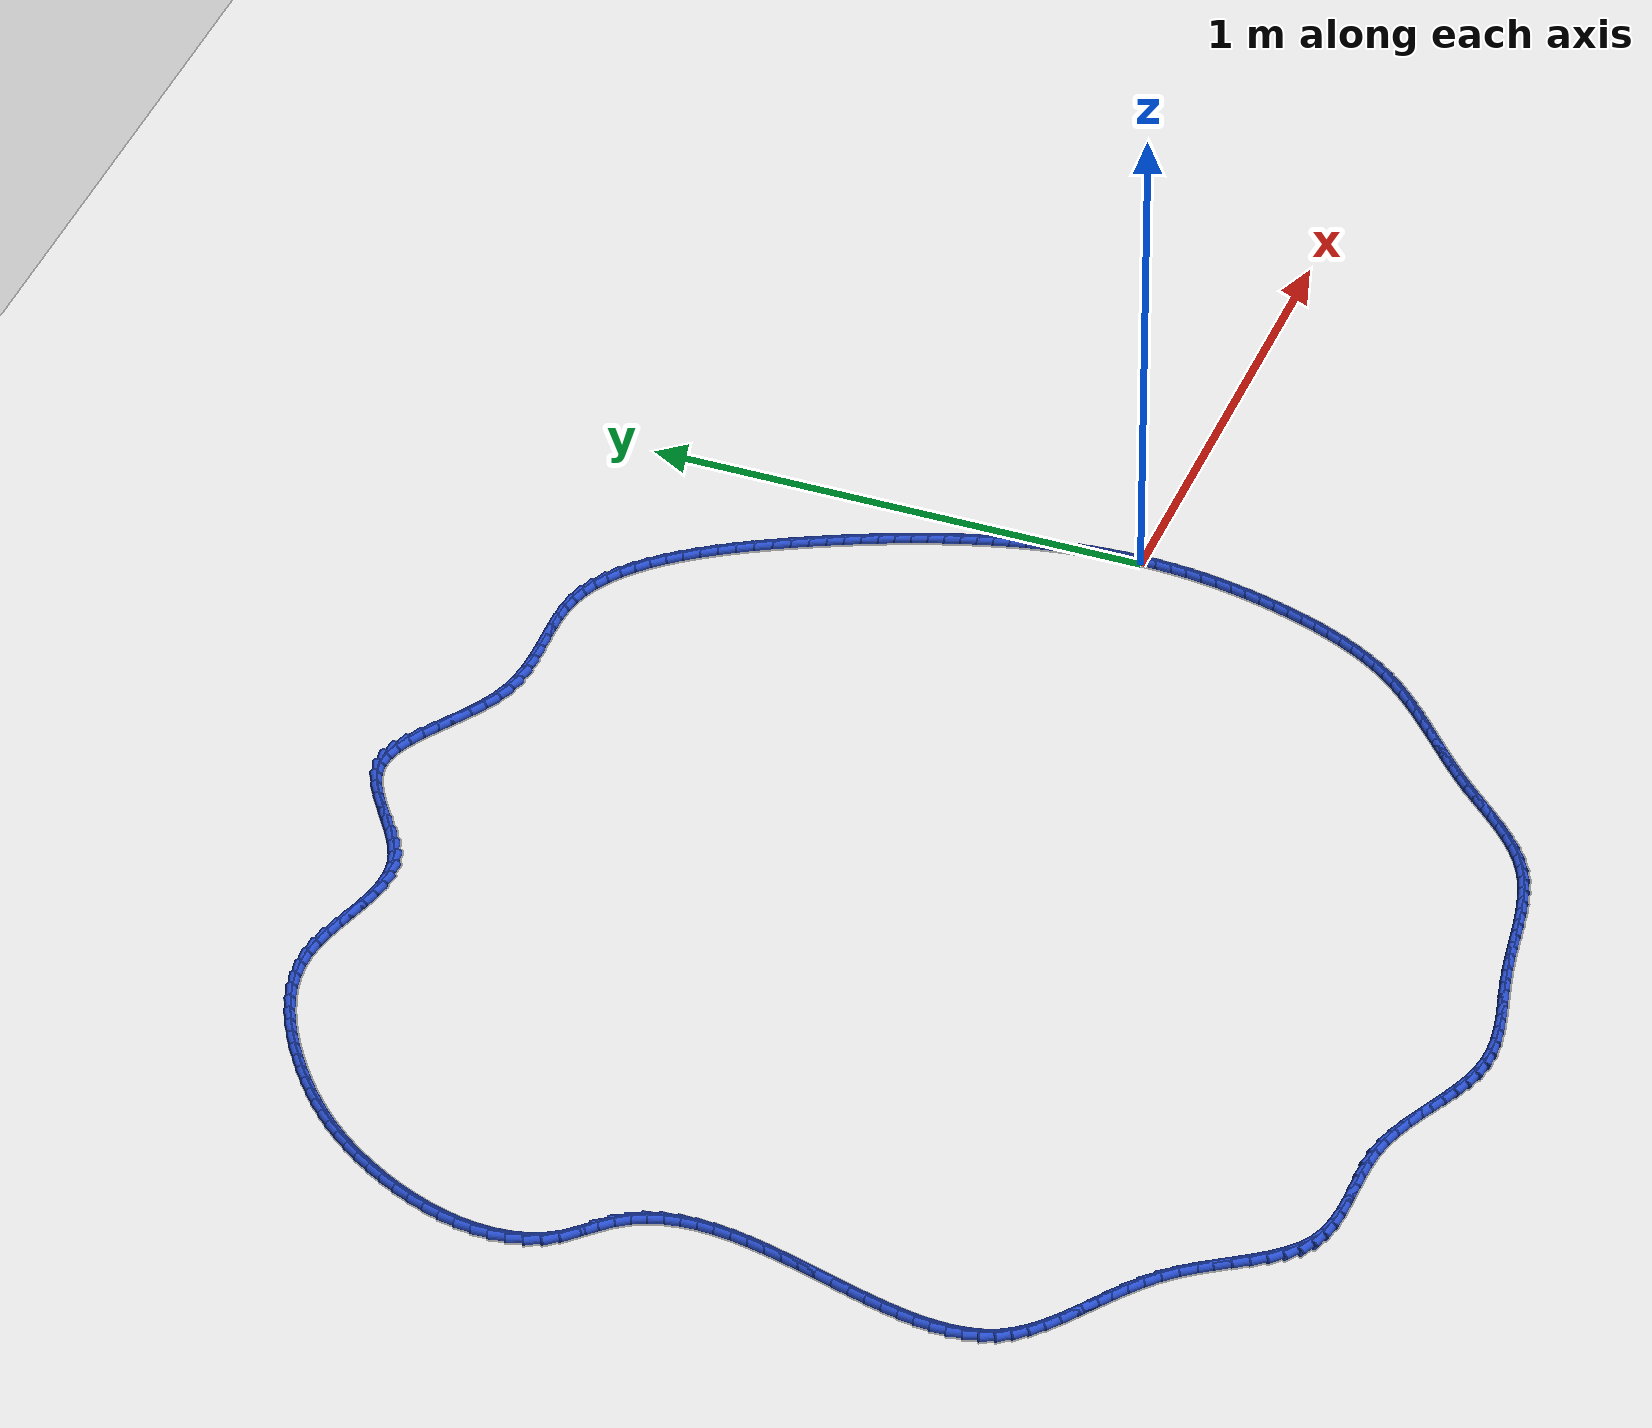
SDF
<sdf version="1.6">
 <world name="default">
  <light name="sun" type="directional">
   <pose>0 0 10 0 -0 0</pose>
   <diffuse>0.8 0.8 0.8 1</diffuse>
   <specular>0.2 0.2 0.2 1</specular>
   <attenuation>
    <range>1000</range>
    <constant>0.9</constant>
    <linear>0.01</linear>
    <quadratic>0.001</quadratic>
   </attenuation>
   <direction>-0.5 0.1 -0.9</direction>
  </light>
  <model name="ground_plane">
   <static>1</static>
   <link name="link">
    <collision name="collision">
     <geometry><plane><normal>0 0 1</normal><size>100 100</size></plane></geometry>
     <surface><friction><ode><mu>100</mu><mu2>50</mu2></ode></friction></surface>
    </collision>
    <visual name="visual">
     <cast_shadows>0</cast_shadows>
     <geometry><plane><normal>0 0 1</normal><size>100 100</size></plane></geometry>
     <material>
      <script><uri>file://media/materials/scripts/gazebo.material</uri><name>Gazebo/WhiteGlow</name></script>
     </material>
    </visual>
   </link>
  </model>
  <gravity>0 0 -9.8</gravity>
  <magnetic_field>6e-06 2.3e-05 -4.2e-05</magnetic_field>
  <atmosphere type="adiabatic"/>
  <physics name="default_physics" default="0" type="ode">
   <max_step_size>0.001</max_step_size>
   <real_time_factor>1</real_time_factor>
   <real_time_update_rate>1000</real_time_update_rate>
  </physics>
  <scene><ambient>0.4 0.4 0.4 1</ambient><background>0.7 0.7 0.7 1</background><shadows>1</shadows></scene>
  <spherical_coordinates>
   <surface_model>EARTH_WGS84</surface_model>
   <latitude_deg>0</latitude_deg>
   <longitude_deg>0</longitude_deg>
   <elevation>0</elevation>
   <heading_deg>0</heading_deg>
  </spherical_coordinates>
  <model name="line">
   <link name="link_0">
    <pose>1.474514954580286e-17 1.457167719820518e-16 0.01 0 1.57 -1.5475321743122046</pose>
    <collision name="collision">
     <geometry><cylinder><radius>0.01</radius><length>0.08</length></cylinder></geometry>
    </collision>
    <visual name="visual">
     <material>
      <script><name>Gazebo/Blue</name><uri>file://media/materials/scripts/gazebo.material</uri></script>
     </material>
     <geometry><cylinder><radius>0.01</radius><length>0.08</length></cylinder></geometry>
    </visual>
   </link>
   <link name="link_1">
    <pose>-0.0007522540752061193 0.03232949745408953 0.01 0 1.57 -1.51250851940609</pose>
    <collision name="collision">
     <geometry><cylinder><radius>0.01</radius><length>0.08</length></cylinder></geometry>
    </collision>
    <visual name="visual">
     <material>
      <script><name>Gazebo/Blue</name><uri>file://media/materials/scripts/gazebo.material</uri></script>
     </material>
     <geometry><cylinder><radius>0.01</radius><length>0.08</length></cylinder></geometry>
    </visual>
   </link>
   <link name="link_2">
    <pose>-0.002640127792043446 0.06468163625894327 0.01 0 1.57 -1.4796041190122342</pose>
    <collision name="collision">
     <geometry><cylinder><radius>0.01</radius><length>0.08</length></cylinder></geometry>
    </collision>
    <visual name="visual">
     <material>
      <script><name>Gazebo/Blue</name><uri>file://media/materials/scripts/gazebo.material</uri></script>
     </material>
     <geometry><cylinder><radius>0.01</radius><length>0.08</length></cylinder></geometry>
    </visual>
   </link>
   <link name="link_3">
    <pose>-0.005595584413329633 0.09700083987464508 0.01 0 1.57 -1.4486975101030588</pose>
    <collision name="collision">
     <geometry><cylinder><radius>0.01</radius><length>0.08</length></cylinder></geometry>
    </collision>
    <visual name="visual">
     <material>
      <script><name>Gazebo/Blue</name><uri>file://media/materials/scripts/gazebo.material</uri></script>
     </material>
     <geometry><cylinder><radius>0.01</radius><length>0.08</length></cylinder></geometry>
    </visual>
   </link>
   <link name="link_4">
    <pose>-0.009550587201882366 0.1292315317612789 0.01 0 1.57 -1.4196662057281555</pose>
    <collision name="collision">
     <geometry><cylinder><radius>0.01</radius><length>0.08</length></cylinder></geometry>
    </collision>
    <visual name="visual">
     <material>
      <script><name>Gazebo/Blue</name><uri>file://media/materials/scripts/gazebo.material</uri></script>
     </material>
     <geometry><cylinder><radius>0.01</radius><length>0.08</length></cylinder></geometry>
    </visual>
   </link>
   <link name="link_5">
    <pose>-0.014437099420519316 0.16131813537892853 0.01 0 1.57 -1.3923894360186462</pose>
    <collision name="collision">
     <geometry><cylinder><radius>0.01</radius><length>0.08</length></cylinder></geometry>
    </collision>
    <visual name="visual">
     <material>
      <script><name>Gazebo/Blue</name><uri>file://media/materials/scripts/gazebo.material</uri></script>
     </material>
     <geometry><cylinder><radius>0.01</radius><length>0.08</length></cylinder></geometry>
    </visual>
   </link>
   <link name="link_6">
    <pose>-0.020187084332058153 0.19320507418767763 0.01 0 1.57 -1.3667501006793694</pose>
    <collision name="collision">
     <geometry><cylinder><radius>0.01</radius><length>0.08</length></cylinder></geometry>
    </collision>
    <visual name="visual">
     <material>
      <script><name>Gazebo/Blue</name><uri>file://media/materials/scripts/gazebo.material</uri></script>
     </material>
     <geometry><cylinder><radius>0.01</radius><length>0.08</length></cylinder></geometry>
    </visual>
   </link>
   <link name="link_7">
    <pose>-0.026732505199316553 0.22483677164761018 0.01 0 1.57 -1.3426360899340068</pose>
    <collision name="collision">
     <geometry><cylinder><radius>0.01</radius><length>0.08</length></cylinder></geometry>
    </collision>
    <visual name="visual">
     <material>
      <script><name>Gazebo/Blue</name><uri>file://media/materials/scripts/gazebo.material</uri></script>
     </material>
     <geometry><cylinder><radius>0.01</radius><length>0.08</length></cylinder></geometry>
    </visual>
   </link>
   <link name="link_8">
    <pose>-0.0340053252851122 0.2561576512188099 0.01 0 1.57 -1.319939995945289</pose>
    <collision name="collision">
     <geometry><cylinder><radius>0.01</radius><length>0.08</length></cylinder></geometry>
    </collision>
    <visual name="visual">
     <material>
      <script><name>Gazebo/Blue</name><uri>file://media/materials/scripts/gazebo.material</uri></script>
     </material>
     <geometry><cylinder><radius>0.01</radius><length>0.08</length></cylinder></geometry>
    </visual>
   </link>
   <link name="link_9">
    <pose>-0.0419375745196763 0.2871122526668698 0.01 0 1.57 -1.2982507750133787</pose>
    <collision name="collision">
     <geometry><cylinder><radius>0.01</radius><length>0.08</length></cylinder></geometry>
    </collision>
    <visual name="visual">
     <material>
      <script><name>Gazebo/Blue</name><uri>file://media/materials/scripts/gazebo.material</uri></script>
     </material>
     <geometry><cylinder><radius>0.01</radius><length>0.08</length></cylinder></geometry>
    </visual>
   </link>
   <link name="link_10">
    <pose>-0.05048127783847042 0.3176799983055524 0.01 0 1.57 -1.2768563255201584</pose>
    <collision name="collision">
     <geometry><cylinder><radius>0.01</radius><length>0.08</length></cylinder></geometry>
    </collision>
    <visual name="visual">
     <material>
      <script><name>Gazebo/Blue</name><uri>file://media/materials/scripts/gazebo.material</uri></script>
     </material>
     <geometry><cylinder><radius>0.01</radius><length>0.08</length></cylinder></geometry>
    </visual>
   </link>
   <link name="link_11">
    <pose>-0.05963636618580562 0.3479238855035927 0.01 0 1.57 -1.255811889309616</pose>
    <collision name="collision">
     <geometry><cylinder><radius>0.01</radius><length>0.08</length></cylinder></geometry>
    </collision>
    <visual name="visual">
     <material>
      <script><name>Gazebo/Blue</name><uri>file://media/materials/scripts/gazebo.material</uri></script>
     </material>
     <geometry><cylinder><radius>0.01</radius><length>0.08</length></cylinder></geometry>
    </visual>
   </link>
   <link name="link_12">
    <pose>-0.06940979589705236 0.3779191678676826 0.01 0 1.57 -1.2352854865000094</pose>
    <collision name="collision">
     <geometry><cylinder><radius>0.01</radius><length>0.08</length></cylinder></geometry>
    </collision>
    <visual name="visual">
     <material>
      <script><name>Gazebo/Blue</name><uri>file://media/materials/scripts/gazebo.material</uri></script>
     </material>
     <geometry><cylinder><radius>0.01</radius><length>0.08</length></cylinder></geometry>
    </visual>
   </link>
   <link name="link_13">
    <pose>-0.07980852330758101 0.40774109900451294 0.01 0 1.57 -1.2154354065618396</pose>
    <collision name="collision">
     <geometry><cylinder><radius>0.01</radius><length>0.08</length></cylinder></geometry>
    </collision>
    <visual name="visual">
     <material>
      <script><name>Gazebo/Blue</name><uri>file://media/materials/scripts/gazebo.material</uri></script>
     </material>
     <geometry><cylinder><radius>0.01</radius><length>0.08</length></cylinder></geometry>
    </visual>
   </link>
   <link name="link_14">
    <pose>-0.090839504752762 0.4374649325207753 0.01 0 1.57 -1.196405954214558</pose>
    <collision name="collision">
     <geometry><cylinder><radius>0.01</radius><length>0.08</length></cylinder></geometry>
    </collision>
    <visual name="visual">
     <material>
      <script><name>Gazebo/Blue</name><uri>file://media/materials/scripts/gazebo.material</uri></script>
     </material>
     <geometry><cylinder><radius>0.01</radius><length>0.08</length></cylinder></geometry>
    </visual>
   </link>
   <link name="link_15">
    <pose>-0.10250969656796577 0.4671659220231611 0.01 0 1.57 -1.1783239818852502</pose>
    <collision name="collision">
     <geometry><cylinder><radius>0.01</radius><length>0.08</length></cylinder></geometry>
    </collision>
    <visual name="visual">
     <material>
      <script><name>Gazebo/Blue</name><uri>file://media/materials/scripts/gazebo.material</uri></script>
     </material>
     <geometry><cylinder><radius>0.01</radius><length>0.08</length></cylinder></geometry>
    </visual>
   </link>
   <link name="link_16">
    <pose>-0.11482605508856275 0.4969193211183616 0.01 0 1.57 -1.1612963700176924</pose>
    <collision name="collision">
     <geometry><cylinder><radius>0.01</radius><length>0.08</length></cylinder></geometry>
    </collision>
    <visual name="visual">
     <material>
      <script><name>Gazebo/Blue</name><uri>file://media/materials/scripts/gazebo.material</uri></script>
     </material>
     <geometry><cylinder><radius>0.01</radius><length>0.08</length></cylinder></geometry>
    </visual>
   </link>
   <link name="link_17">
    <pose>-0.12779553664992332 0.5268003834130682 0.01 0 1.57 -1.1454085234126348</pose>
    <collision name="collision">
     <geometry><cylinder><radius>0.01</radius><length>0.08</length></cylinder></geometry>
    </collision>
    <visual name="visual">
     <material>
      <script><name>Gazebo/Blue</name><uri>file://media/materials/scripts/gazebo.material</uri></script>
     </material>
     <geometry><cylinder><radius>0.01</radius><length>0.08</length></cylinder></geometry>
    </visual>
   </link>
   <link name="link_18">
    <pose>-0.1414250975874179 0.5568843625139722 0.01 0 1.57 -1.1307238626450877</pose>
    <collision name="collision">
     <geometry><cylinder><radius>0.01</radius><length>0.08</length></cylinder></geometry>
    </collision>
    <visual name="visual">
     <material>
      <script><name>Gazebo/Blue</name><uri>file://media/materials/scripts/gazebo.material</uri></script>
     </material>
     <geometry><cylinder><radius>0.01</radius><length>0.08</length></cylinder></geometry>
    </visual>
   </link>
   <link name="link_19">
    <pose>-0.15572169423641688 0.587246512027765 0.01 0 1.57 -1.117283887355243</pose>
    <collision name="collision">
     <geometry><cylinder><radius>0.01</radius><length>0.08</length></cylinder></geometry>
    </collision>
    <visual name="visual">
     <material>
      <script><name>Gazebo/Blue</name><uri>file://media/materials/scripts/gazebo.material</uri></script>
     </material>
     <geometry><cylinder><radius>0.01</radius><length>0.08</length></cylinder></geometry>
    </visual>
   </link>
   <link name="link_20">
    <pose>-0.17069228479510767 0.6179620637843862 0.01 0 1.57 -1.104023860555358</pose>
    <collision name="collision">
     <geometry><cylinder><radius>0.01</radius><length>0.08</length></cylinder></geometry>
    </collision>
    <visual name="visual">
     <material>
      <script><name>Gazebo/Blue</name><uri>file://media/materials/scripts/gazebo.material</uri></script>
     </material>
     <geometry><cylinder><radius>0.01</radius><length>0.08</length></cylinder></geometry>
    </visual>
   </link>
   <link name="link_21">
    <pose>-0.18634997945250809 0.6490343314463008 0.01 0 1.57 -1.0874084788218168</pose>
    <collision name="collision">
     <geometry><cylinder><radius>0.01</radius><length>0.08</length></cylinder></geometry>
    </collision>
    <visual name="visual">
     <material>
      <script><name>Gazebo/Blue</name><uri>file://media/materials/scripts/gazebo.material</uri></script>
     </material>
     <geometry><cylinder><radius>0.01</radius><length>0.08</length></cylinder></geometry>
    </visual>
   </link>
   <link name="link_22">
    <pose>-0.2027277406531573 0.6802345513083949 0.01 0 1.57 -1.0665742777429101</pose>
    <collision name="collision">
     <geometry><cylinder><radius>0.01</radius><length>0.08</length></cylinder></geometry>
    </collision>
    <visual name="visual">
     <material>
      <script><name>Gazebo/Blue</name><uri>file://media/materials/scripts/gazebo.material</uri></script>
     </material>
     <geometry><cylinder><radius>0.01</radius><length>0.08</length></cylinder></geometry>
    </visual>
   </link>
   <link name="link_23">
    <pose>-0.21986252773545875 0.7112872350701809 0.01 0 1.57 -1.041225801698727</pose>
    <collision name="collision">
     <geometry><cylinder><radius>0.01</radius><length>0.08</length></cylinder></geometry>
    </collision>
    <visual name="visual">
     <material>
      <script><name>Gazebo/Blue</name><uri>file://media/materials/scripts/gazebo.material</uri></script>
     </material>
     <geometry><cylinder><radius>0.01</radius><length>0.08</length></cylinder></geometry>
    </visual>
   </link>
   <link name="link_24">
    <pose>-0.2377913000378159 0.7419168944311705 0.01 0 1.57 -1.0109306822628294</pose>
    <collision name="collision">
     <geometry><cylinder><radius>0.01</radius><length>0.08</length></cylinder></geometry>
    </collision>
    <visual name="visual">
     <material>
      <script><name>Gazebo/Blue</name><uri>file://media/materials/scripts/gazebo.material</uri></script>
     </material>
     <geometry><cylinder><radius>0.01</radius><length>0.08</length></cylinder></geometry>
    </visual>
   </link>
   <link name="link_25">
    <pose>-0.25655101689863197 0.7718480410908758 0.01 0 1.57 -0.9751145238123848</pose>
    <collision name="collision">
     <geometry><cylinder><radius>0.01</radius><length>0.08</length></cylinder></geometry>
    </collision>
    <visual name="visual">
     <material>
      <script><name>Gazebo/Blue</name><uri>file://media/materials/scripts/gazebo.material</uri></script>
     </material>
     <geometry><cylinder><radius>0.01</radius><length>0.08</length></cylinder></geometry>
    </visual>
   </link>
   <link name="link_26">
    <pose>-0.2761786376563105 0.8008051867488085 0.01 0 1.57 -0.93305426914714</pose>
    <collision name="collision">
     <geometry><cylinder><radius>0.01</radius><length>0.08</length></cylinder></geometry>
    </collision>
    <visual name="visual">
     <material>
      <script><name>Gazebo/Blue</name><uri>file://media/materials/scripts/gazebo.material</uri></script>
     </material>
     <geometry><cylinder><radius>0.01</radius><length>0.08</length></cylinder></geometry>
    </visual>
   </link>
   <link name="link_27">
    <pose>-0.2967111216492549 0.8285128431044805 0.01 0 1.57 -0.8838756895190978</pose>
    <collision name="collision">
     <geometry><cylinder><radius>0.01</radius><length>0.08</length></cylinder></geometry>
    </collision>
    <visual name="visual">
     <material>
      <script><name>Gazebo/Blue</name><uri>file://media/materials/scripts/gazebo.material</uri></script>
     </material>
     <geometry><cylinder><radius>0.01</radius><length>0.08</length></cylinder></geometry>
    </visual>
   </link>
   <link name="link_28">
    <pose>-0.3181854282158685 0.8546955218574042 0.01 0 1.57 -0.826564430199759</pose>
    <collision name="collision">
     <geometry><cylinder><radius>0.01</radius><length>0.08</length></cylinder></geometry>
    </collision>
    <visual name="visual">
     <material>
      <script><name>Gazebo/Blue</name><uri>file://media/materials/scripts/gazebo.material</uri></script>
     </material>
     <geometry><cylinder><radius>0.01</radius><length>0.08</length></cylinder></geometry>
    </visual>
   </link>
   <link name="link_29">
    <pose>-0.3406385166945547 0.8790777347070909 0.01 0 1.57 -0.7600061596608447</pose>
    <collision name="collision">
     <geometry><cylinder><radius>0.01</radius><length>0.08</length></cylinder></geometry>
    </collision>
    <visual name="visual">
     <material>
      <script><name>Gazebo/Blue</name><uri>file://media/materials/scripts/gazebo.material</uri></script>
     </material>
     <geometry><cylinder><radius>0.01</radius><length>0.08</length></cylinder></geometry>
    </visual>
   </link>
   <link name="link_30">
    <pose>-0.36410734642371706 0.901383993353053 0.01 0 1.57 -0.6830793605900667</pose>
    <collision name="collision">
     <geometry><cylinder><radius>0.01</radius><length>0.08</length></cylinder></geometry>
    </collision>
    <visual name="visual">
     <material>
      <script><name>Gazebo/Blue</name><uri>file://media/materials/scripts/gazebo.material</uri></script>
     </material>
     <geometry><cylinder><radius>0.01</radius><length>0.08</length></cylinder></geometry>
    </visual>
   </link>
   <link name="link_31">
    <pose>-0.3886288767417589 0.9213388094948021 0.01 0 1.57 -0.5948307333020056</pose>
    <collision name="collision">
     <geometry><cylinder><radius>0.01</radius><length>0.08</length></cylinder></geometry>
    </collision>
    <visual name="visual">
     <material>
      <script><name>Gazebo/Blue</name><uri>file://media/materials/scripts/gazebo.material</uri></script>
     </material>
     <geometry><cylinder><radius>0.01</radius><length>0.08</length></cylinder></geometry>
    </visual>
   </link>
   <link name="link_32">
    <pose>-0.4142400669870835 0.9386666948318501 0.01 0 1.57 -0.49475817461183097</pose>
    <collision name="collision">
     <geometry><cylinder><radius>0.01</radius><length>0.08</length></cylinder></geometry>
    </collision>
    <visual name="visual">
     <material>
      <script><name>Gazebo/Blue</name><uri>file://media/materials/scripts/gazebo.material</uri></script>
     </material>
     <geometry><cylinder><radius>0.01</radius><length>0.08</length></cylinder></geometry>
    </visual>
   </link>
   <link name="link_33">
    <pose>-0.44097787649809433 0.9530921610637092 0.01 0 1.57 -0.38319163222508473</pose>
    <collision name="collision">
     <geometry><cylinder><radius>0.01</radius><length>0.08</length></cylinder></geometry>
    </collision>
    <visual name="visual">
     <material>
      <script><name>Gazebo/Blue</name><uri>file://media/materials/scripts/gazebo.material</uri></script>
     </material>
     <geometry><cylinder><radius>0.01</radius><length>0.08</length></cylinder></geometry>
    </visual>
   </link>
   <link name="link_34">
    <pose>-0.46887926461319485 0.9643397198898909 0.01 0 1.57 -0.26172835505001213</pose>
    <collision name="collision">
     <geometry><cylinder><radius>0.01</radius><length>0.08</length></cylinder></geometry>
    </collision>
    <visual name="visual">
     <material>
      <script><name>Gazebo/Blue</name><uri>file://media/materials/scripts/gazebo.material</uri></script>
     </material>
     <geometry><cylinder><radius>0.01</radius><length>0.08</length></cylinder></geometry>
    </visual>
   </link>
   <link name="link_35">
    <pose>-0.4979808915021397 0.972135261770793 0.01 0 1.57 -0.14386309632848734</pose>
    <collision name="collision">
     <geometry><cylinder><radius>0.01</radius><length>0.08</length></cylinder></geometry>
    </collision>
    <visual name="visual">
     <material>
      <script><name>Gazebo/Blue</name><uri>file://media/materials/scripts/gazebo.material</uri></script>
     </material>
     <geometry><cylinder><radius>0.01</radius><length>0.08</length></cylinder></geometry>
    </visual>
   </link>
   <link name="link_36">
    <pose>-0.5282509329211491 0.9765202972394422 0.01 0 1.57 -0.05536648467017081</pose>
    <collision name="collision">
     <geometry><cylinder><radius>0.01</radius><length>0.08</length></cylinder></geometry>
    </collision>
    <visual name="visual">
     <material>
      <script><name>Gazebo/Blue</name><uri>file://media/materials/scripts/gazebo.material</uri></script>
     </material>
     <geometry><cylinder><radius>0.01</radius><length>0.08</length></cylinder></geometry>
    </visual>
   </link>
   <link name="link_37">
    <pose>-0.5595022035116406 0.9782523404245301 0.01 0 1.57 0.0020202784681673824</pose>
    <collision name="collision">
     <geometry><cylinder><radius>0.01</radius><length>0.08</length></cylinder></geometry>
    </collision>
    <visual name="visual">
     <material>
      <script><name>Gazebo/Blue</name><uri>file://media/materials/scripts/gazebo.material</uri></script>
     </material>
     <geometry><cylinder><radius>0.01</radius><length>0.08</length></cylinder></geometry>
    </visual>
   </link>
   <link name="link_38">
    <pose>-0.5915260934414077 0.9781876431612169 0.01 0 1.57 0.030835594973835437</pose>
    <collision name="collision">
     <geometry><cylinder><radius>0.01</radius><length>0.08</length></cylinder></geometry>
    </collision>
    <visual name="visual">
     <material>
      <script><name>Gazebo/Blue</name><uri>file://media/materials/scripts/gazebo.material</uri></script>
     </material>
     <geometry><cylinder><radius>0.01</radius><length>0.08</length></cylinder></geometry>
    </visual>
   </link>
   <link name="link_39">
    <pose>-0.6241139928782442 0.9771824572846628 0.01 0 1.57 0.03305758115891684</pose>
    <collision name="collision">
     <geometry><cylinder><radius>0.01</radius><length>0.08</length></cylinder></geometry>
    </collision>
    <visual name="visual">
     <material>
      <script><name>Gazebo/Blue</name><uri>file://media/materials/scripts/gazebo.material</uri></script>
     </material>
     <geometry><cylinder><radius>0.01</radius><length>0.08</length></cylinder></geometry>
    </visual>
   </link>
   <link name="link_40">
    <pose>-0.6570572919899436 0.9760930346300285 0.01 0 1.57 0.009591931395367972</pose>
    <collision name="collision">
     <geometry><cylinder><radius>0.01</radius><length>0.08</length></cylinder></geometry>
    </collision>
    <visual name="visual">
     <material>
      <script><name>Gazebo/Blue</name><uri>file://media/materials/scripts/gazebo.material</uri></script>
     </material>
     <geometry><cylinder><radius>0.01</radius><length>0.08</length></cylinder></geometry>
    </visual>
   </link>
   <link name="link_41">
    <pose>-0.6901473809442994 0.9757756270324743 0.01 0 1.57 -0.03966818998932322</pose>
    <collision name="collision">
     <geometry><cylinder><radius>0.01</radius><length>0.08</length></cylinder></geometry>
    </collision>
    <visual name="visual">
     <material>
      <script><name>Gazebo/Blue</name><uri>file://media/materials/scripts/gazebo.material</uri></script>
     </material>
     <geometry><cylinder><radius>0.01</radius><length>0.08</length></cylinder></geometry>
    </visual>
   </link>
   <link name="link_42">
    <pose>-0.7231756499091058 0.9770864863271609 0.01 0 1.57 -0.11534736876464292</pose>
    <collision name="collision">
     <geometry><cylinder><radius>0.01</radius><length>0.08</length></cylinder></geometry>
    </collision>
    <visual name="visual">
     <material>
      <script><name>Gazebo/Blue</name><uri>file://media/materials/scripts/gazebo.material</uri></script>
     </material>
     <geometry><cylinder><radius>0.01</radius><length>0.08</length></cylinder></geometry>
    </visual>
   </link>
   <link name="link_43">
    <pose>-0.755933489052156 0.9808818643492483 0.01 0 1.57 -0.21757878261661803</pose>
    <collision name="collision">
     <geometry><cylinder><radius>0.01</radius><length>0.08</length></cylinder></geometry>
    </collision>
    <visual name="visual">
     <material>
      <script><name>Gazebo/Blue</name><uri>file://media/materials/scripts/gazebo.material</uri></script>
     </material>
     <geometry><cylinder><radius>0.01</radius><length>0.08</length></cylinder></geometry>
    </visual>
   </link>
   <link name="link_44">
    <pose>-0.7882122885412435 0.9880180129338967 0.01 0 1.57 -0.3421504435039345</pose>
    <collision name="collision">
     <geometry><cylinder><radius>0.01</radius><length>0.08</length></cylinder></geometry>
    </collision>
    <visual name="visual">
     <material>
      <script><name>Gazebo/Blue</name><uri>file://media/materials/scripts/gazebo.material</uri></script>
     </material>
     <geometry><cylinder><radius>0.01</radius><length>0.08</length></cylinder></geometry>
    </visual>
   </link>
   <link name="link_45">
    <pose>-0.8198141549782639 0.9992732784349818 0.01 0 1.57 -0.4526314392853402</pose>
    <collision name="collision">
     <geometry><cylinder><radius>0.01</radius><length>0.08</length></cylinder></geometry>
    </collision>
    <visual name="visual">
     <material>
      <script><name>Gazebo/Blue</name><uri>file://media/materials/scripts/gazebo.material</uri></script>
     </material>
     <geometry><cylinder><radius>0.01</radius><length>0.08</length></cylinder></geometry>
    </visual>
   </link>
   <link name="link_46">
    <pose>-0.8506972060312612 1.0142918503517326 0.01 0 1.57 -0.5263132004046575</pose>
    <collision name="collision">
     <geometry><cylinder><radius>0.01</radius><length>0.08</length></cylinder></geometry>
    </collision>
    <visual name="visual">
     <material>
      <script><name>Gazebo/Blue</name><uri>file://media/materials/scripts/gazebo.material</uri></script>
     </material>
     <geometry><cylinder><radius>0.01</radius><length>0.08</length></cylinder></geometry>
    </visual>
   </link>
   <link name="link_47">
    <pose>-0.8809374760276731 1.031860697020608 0.01 0 1.57 -0.5667276058517842</pose>
    <collision name="collision">
     <geometry><cylinder><radius>0.01</radius><length>0.08</length></cylinder></geometry>
    </collision>
    <visual name="visual">
     <material>
      <script><name>Gazebo/Blue</name><uri>file://media/materials/scripts/gazebo.material</uri></script>
     </material>
     <geometry><cylinder><radius>0.01</radius><length>0.08</length></cylinder></geometry>
    </visual>
   </link>
   <link name="link_48">
    <pose>-0.910613909178522 1.050745632737551 0.01 0 1.57 -0.5761906763435826</pose>
    <collision name="collision">
     <geometry><cylinder><radius>0.01</radius><length>0.08</length></cylinder></geometry>
    </collision>
    <visual name="visual">
     <material>
      <script><name>Gazebo/Blue</name><uri>file://media/materials/scripts/gazebo.material</uri></script>
     </material>
     <geometry><cylinder><radius>0.01</radius><length>0.08</length></cylinder></geometry>
    </visual>
   </link>
   <link name="link_49">
    <pose>-0.9398054496948308 1.0697124717985054 0.01 0 1.57 -0.5541795112804764</pose>
    <collision name="collision">
     <geometry><cylinder><radius>0.01</radius><length>0.08</length></cylinder></geometry>
    </collision>
    <visual name="visual">
     <material>
      <script><name>Gazebo/Blue</name><uri>file://media/materials/scripts/gazebo.material</uri></script>
     </material>
     <geometry><cylinder><radius>0.01</radius><length>0.08</length></cylinder></geometry>
    </visual>
   </link>
   <link name="link_50">
    <pose>-0.9685910417876222 1.0875270284994147 0.01 0 1.57 -0.4967764145526951</pose>
    <collision name="collision">
     <geometry><cylinder><radius>0.01</radius><length>0.08</length></cylinder></geometry>
    </collision>
    <visual name="visual">
     <material>
      <script><name>Gazebo/Blue</name><uri>file://media/materials/scripts/gazebo.material</uri></script>
     </material>
     <geometry><cylinder><radius>0.01</radius><length>0.08</length></cylinder></geometry>
    </visual>
   </link>
   <link name="link_51">
    <pose>-0.9970496296679189 1.1029551171362217 0.01 0 1.57 -0.3963923191846263</pose>
    <collision name="collision">
     <geometry><cylinder><radius>0.01</radius><length>0.08</length></cylinder></geometry>
    </collision>
    <visual name="visual">
     <material>
      <script><name>Gazebo/Blue</name><uri>file://media/materials/scripts/gazebo.material</uri></script>
     </material>
     <geometry><cylinder><radius>0.01</radius><length>0.08</length></cylinder></geometry>
    </visual>
   </link>
   <link name="link_52">
    <pose>-1.0252601575467433 1.1147625520048705 0.01 0 1.57 -0.24303915994346564</pose>
    <collision name="collision">
     <geometry><cylinder><radius>0.01</radius><length>0.08</length></cylinder></geometry>
    </collision>
    <visual name="visual">
     <material>
      <script><name>Gazebo/Blue</name><uri>file://media/materials/scripts/gazebo.material</uri></script>
     </material>
     <geometry><cylinder><radius>0.01</radius><length>0.08</length></cylinder></geometry>
    </visual>
   </link>
   <link name="link_53">
    <pose>-1.0533015696351185 1.121715147401304 0.01 0 1.57 -0.03088749037135459</pose>
    <collision name="collision">
     <geometry><cylinder><radius>0.01</radius><length>0.08</length></cylinder></geometry>
    </collision>
    <visual name="visual">
     <material>
      <script><name>Gazebo/Blue</name><uri>file://media/materials/scripts/gazebo.material</uri></script>
     </material>
     <geometry><cylinder><radius>0.01</radius><length>0.08</length></cylinder></geometry>
    </visual>
   </link>
   <link name="link_54">
    <pose>-1.0812528098690035 1.1225787657236606 0.01 0 1.57 0.2093572465290852</pose>
    <collision name="collision">
     <geometry><cylinder><radius>0.01</radius><length>0.08</length></cylinder></geometry>
    </collision>
    <visual name="visual">
     <material>
      <script><name>Gazebo/Blue</name><uri>file://media/materials/scripts/gazebo.material</uri></script>
     </material>
     <geometry><cylinder><radius>0.01</radius><length>0.08</length></cylinder></geometry>
    </visual>
   </link>
   <link name="link_55">
    <pose>-1.1091898274913934 1.1166429713087278 0.01 0 1.57 0.39373224120965816</pose>
    <collision name="collision">
     <geometry><cylinder><radius>0.01</radius><length>0.08</length></cylinder></geometry>
    </collision>
    <visual name="visual">
     <material>
      <script><name>Gazebo/Blue</name><uri>file://media/materials/scripts/gazebo.material</uri></script>
     </material>
     <geometry><cylinder><radius>0.01</radius><length>0.08</length></cylinder></geometry>
    </visual>
   </link>
   <link name="link_56">
    <pose>-1.1371781724248873 1.1050159270338085 0.01 0 1.57 0.51259802211965</pose>
    <collision name="collision">
     <geometry><cylinder><radius>0.01</radius><length>0.08</length></cylinder></geometry>
    </collision>
    <visual name="visual">
     <material>
      <script><name>Gazebo/Blue</name><uri>file://media/materials/scripts/gazebo.material</uri></script>
     </material>
     <geometry><cylinder><radius>0.01</radius><length>0.08</length></cylinder></geometry>
    </visual>
   </link>
   <link name="link_57">
    <pose>-1.1652811387390374 1.0892002918491626 0.01 0 1.57 0.5793274111684797</pose>
    <collision name="collision">
     <geometry><cylinder><radius>0.01</radius><length>0.08</length></cylinder></geometry>
    </collision>
    <visual name="visual">
     <material>
      <script><name>Gazebo/Blue</name><uri>file://media/materials/scripts/gazebo.material</uri></script>
     </material>
     <geometry><cylinder><radius>0.01</radius><length>0.08</length></cylinder></geometry>
    </visual>
   </link>
   <link name="link_58">
    <pose>-1.1935620205033939 1.0706987247050515 0.01 0 1.57 0.6040921626146539</pose>
    <collision name="collision">
     <geometry><cylinder><radius>0.01</radius><length>0.08</length></cylinder></geometry>
    </collision>
    <visual name="visual">
     <material>
      <script><name>Gazebo/Blue</name><uri>file://media/materials/scripts/gazebo.material</uri></script>
     </material>
     <geometry><cylinder><radius>0.01</radius><length>0.08</length></cylinder></geometry>
    </visual>
   </link>
   <link name="link_59">
    <pose>-1.22208411178751 1.0510138845517356 0.01 0 1.57 0.591542006042264</pose>
    <collision name="collision">
     <geometry><cylinder><radius>0.01</radius><length>0.08</length></cylinder></geometry>
    </collision>
    <visual name="visual">
     <material>
      <script><name>Gazebo/Blue</name><uri>file://media/materials/scripts/gazebo.material</uri></script>
     </material>
     <geometry><cylinder><radius>0.01</radius><length>0.08</length></cylinder></geometry>
    </visual>
   </link>
   <link name="link_60">
    <pose>-1.2509107066609366 1.0316484303394766 0.01 0 1.57 0.5410935562170069</pose>
    <collision name="collision">
     <geometry><cylinder><radius>0.01</radius><length>0.08</length></cylinder></geometry>
    </collision>
    <visual name="visual">
     <material>
      <script><name>Gazebo/Blue</name><uri>file://media/materials/scripts/gazebo.material</uri></script>
     </material>
     <geometry><cylinder><radius>0.01</radius><length>0.08</length></cylinder></geometry>
    </visual>
   </link>
   <link name="link_61">
    <pose>-1.2801050991932266 1.0141050210185352 0.01 0 1.57 0.4474780836240453</pose>
    <collision name="collision">
     <geometry><cylinder><radius>0.01</radius><length>0.08</length></cylinder></geometry>
    </collision>
    <visual name="visual">
     <material>
      <script><name>Gazebo/Blue</name><uri>file://media/materials/scripts/gazebo.material</uri></script>
     </material>
     <geometry><cylinder><radius>0.01</radius><length>0.08</length></cylinder></geometry>
    </visual>
   </link>
   <link name="link_62">
    <pose>-1.3097305834539301 0.999886315539172 0.01 0 1.57 0.3022547152007498</pose>
    <collision name="collision">
     <geometry><cylinder><radius>0.01</radius><length>0.08</length></cylinder></geometry>
    </collision>
    <visual name="visual">
     <material>
      <script><name>Gazebo/Blue</name><uri>file://media/materials/scripts/gazebo.material</uri></script>
     </material>
     <geometry><cylinder><radius>0.01</radius><length>0.08</length></cylinder></geometry>
    </visual>
   </link>
   <link name="link_63">
    <pose>-1.3398504391144583 0.9904946901964533 0.01 0 1.57 0.11792265164271877</pose>
    <collision name="collision">
     <geometry><cylinder><radius>0.01</radius><length>0.08</length></cylinder></geometry>
    </collision>
    <visual name="visual">
     <material>
      <script><name>Gazebo/Blue</name><uri>file://media/materials/scripts/gazebo.material</uri></script>
     </material>
     <geometry><cylinder><radius>0.01</radius><length>0.08</length></cylinder></geometry>
    </visual>
   </link>
   <link name="link_64">
    <pose>-1.3704989701059427 0.9868636879240502 0.01 0 1.57 -0.041806255450858934</pose>
    <collision name="collision">
     <geometry><cylinder><radius>0.01</radius><length>0.08</length></cylinder></geometry>
    </collision>
    <visual name="visual">
     <material>
      <script><name>Gazebo/Blue</name><uri>file://media/materials/scripts/gazebo.material</uri></script>
     </material>
     <geometry><cylinder><radius>0.01</radius><length>0.08</length></cylinder></geometry>
    </visual>
   </link>
   <link name="link_65">
    <pose>-1.401620760689415 0.9881655319779445 0.01 0 1.57 -0.15938130991238214</pose>
    <collision name="collision">
     <geometry><cylinder><radius>0.01</radius><length>0.08</length></cylinder></geometry>
    </collision>
    <visual name="visual">
     <material>
      <script><name>Gazebo/Blue</name><uri>file://media/materials/scripts/gazebo.material</uri></script>
     </material>
     <geometry><cylinder><radius>0.01</radius><length>0.08</length></cylinder></geometry>
    </visual>
   </link>
   <link name="link_66">
    <pose>-1.4331430826894918 0.9932325788391437 0.01 0 1.57 -0.23615573508660329</pose>
    <collision name="collision">
     <geometry><cylinder><radius>0.01</radius><length>0.08</length></cylinder></geometry>
    </collision>
    <visual name="visual">
     <material>
      <script><name>Gazebo/Blue</name><uri>file://media/materials/scripts/gazebo.material</uri></script>
     </material>
     <geometry><cylinder><radius>0.01</radius><length>0.08</length></cylinder></geometry>
    </visual>
   </link>
   <link name="link_67">
    <pose>-1.4649932079307877 1.0008971849886539 0.01 0 1.57 -0.27604075094024194</pose>
    <collision name="collision">
     <geometry><cylinder><radius>0.01</radius><length>0.08</length></cylinder></geometry>
    </collision>
    <visual name="visual">
     <material>
      <script><name>Gazebo/Blue</name><uri>file://media/materials/scripts/gazebo.material</uri></script>
     </material>
     <geometry><cylinder><radius>0.01</radius><length>0.08</length></cylinder></geometry>
    </visual>
   </link>
   <link name="link_68">
    <pose>-1.497098408237919 1.0099917069074826 0.01 0 1.57 -0.2820690126569413</pose>
    <collision name="collision">
     <geometry><cylinder><radius>0.01</radius><length>0.08</length></cylinder></geometry>
    </collision>
    <visual name="visual">
     <material>
      <script><name>Gazebo/Blue</name><uri>file://media/materials/scripts/gazebo.material</uri></script>
     </material>
     <geometry><cylinder><radius>0.01</radius><length>0.08</length></cylinder></geometry>
    </visual>
   </link>
   <link name="link_69">
    <pose>-1.5293859554355 1.019348501076636 0.01 0 1.57 -0.25518205291023527</pose>
    <collision name="collision">
     <geometry><cylinder><radius>0.01</radius><length>0.08</length></cylinder></geometry>
    </collision>
    <visual name="visual">
     <material>
      <script><name>Gazebo/Blue</name><uri>file://media/materials/scripts/gazebo.material</uri></script>
     </material>
     <geometry><cylinder><radius>0.01</radius><length>0.08</length></cylinder></geometry>
    </visual>
   </link>
   <link name="link_70">
    <pose>-1.5617831213481475 1.0277999239771214 0.01 0 1.57 -0.19417978867634483</pose>
    <collision name="collision">
     <geometry><cylinder><radius>0.01</radius><length>0.08</length></cylinder></geometry>
    </collision>
    <visual name="visual">
     <material>
      <script><name>Gazebo/Blue</name><uri>file://media/materials/scripts/gazebo.material</uri></script>
     </material>
     <geometry><cylinder><radius>0.01</radius><length>0.08</length></cylinder></geometry>
    </visual>
   </link>
   <link name="link_71">
    <pose>-1.5942171778004763 1.0341783320899458 0.01 0 1.57 -0.0970384240240674</pose>
    <collision name="collision">
     <geometry><cylinder><radius>0.01</radius><length>0.08</length></cylinder></geometry>
    </collision>
    <visual name="visual">
     <material>
      <script><name>Gazebo/Blue</name><uri>file://media/materials/scripts/gazebo.material</uri></script>
     </material>
     <geometry><cylinder><radius>0.01</radius><length>0.08</length></cylinder></geometry>
    </visual>
   </link>
   <link name="link_72">
    <pose>-1.6266150696507446 1.0373320777119834 0.01 0 1.57 0.018456018644051532</pose>
    <collision name="collision">
     <geometry><cylinder><radius>0.01</radius><length>0.08</length></cylinder></geometry>
    </collision>
    <visual name="visual">
     <material>
      <script><name>Gazebo/Blue</name><uri>file://media/materials/scripts/gazebo.material</uri></script>
     </material>
     <geometry><cylinder><radius>0.01</radius><length>0.08</length></cylinder></geometry>
    </visual>
   </link>
   <link name="link_73">
    <pose>-1.658890929232659 1.036736326201706 0.01 0 1.57 0.12578425098897594</pose>
    <collision name="collision">
     <geometry><cylinder><radius>0.01</radius><length>0.08</length></cylinder></geometry>
    </collision>
    <visual name="visual">
     <material>
      <script><name>Gazebo/Blue</name><uri>file://media/materials/scripts/gazebo.material</uri></script>
     </material>
     <geometry><cylinder><radius>0.01</radius><length>0.08</length></cylinder></geometry>
    </visual>
   </link>
   <link name="link_74">
    <pose>-1.6909421858778233 1.0326833855378892 0.01 0 1.57 0.2220720010524591</pose>
    <collision name="collision">
     <geometry><cylinder><radius>0.01</radius><length>0.08</length></cylinder></geometry>
    </collision>
    <visual name="visual">
     <material>
      <script><name>Gazebo/Blue</name><uri>file://media/materials/scripts/gazebo.material</uri></script>
     </material>
     <geometry><cylinder><radius>0.01</radius><length>0.08</length></cylinder></geometry>
    </visual>
   </link>
   <link name="link_75">
    <pose>-1.722665146665327 1.0255204664261497 0.01 0 1.57 0.30716650345870583</pose>
    <collision name="collision">
     <geometry><cylinder><radius>0.01</radius><length>0.08</length></cylinder></geometry>
    </collision>
    <visual name="visual">
     <material>
      <script><name>Gazebo/Blue</name><uri>file://media/materials/scripts/gazebo.material</uri></script>
     </material>
     <geometry><cylinder><radius>0.01</radius><length>0.08</length></cylinder></geometry>
    </visual>
   </link>
   <link name="link_76">
    <pose>-1.7539561186742578 1.0155947795721028 0.01 0 1.57 0.3816026447308848</pose>
    <collision name="collision">
     <geometry><cylinder><radius>0.01</radius><length>0.08</length></cylinder></geometry>
    </collision>
    <visual name="visual">
     <material>
      <script><name>Gazebo/Blue</name><uri>file://media/materials/scripts/gazebo.material</uri></script>
     </material>
     <geometry><cylinder><radius>0.01</radius><length>0.08</length></cylinder></geometry>
    </visual>
   </link>
   <link name="link_77">
    <pose>-1.7847114089837033 1.0032535356813657 0.01 0 1.57 0.4462764927679804</pose>
    <collision name="collision">
     <geometry><cylinder><radius>0.01</radius><length>0.08</length></cylinder></geometry>
    </collision>
    <visual name="visual">
     <material>
      <script><name>Gazebo/Blue</name><uri>file://media/materials/scripts/gazebo.material</uri></script>
     </material>
     <geometry><cylinder><radius>0.01</radius><length>0.08</length></cylinder></geometry>
    </visual>
   </link>
   <link name="link_78">
    <pose>-1.814827324672753 0.9888439454595546 0.01 0 1.57 0.5022067671707312</pose>
    <collision name="collision">
     <geometry><cylinder><radius>0.01</radius><length>0.08</length></cylinder></geometry>
    </collision>
    <visual name="visual">
     <material>
      <script><name>Gazebo/Blue</name><uri>file://media/materials/scripts/gazebo.material</uri></script>
     </material>
     <geometry><cylinder><radius>0.01</radius><length>0.08</length></cylinder></geometry>
    </visual>
   </link>
   <link name="link_79">
    <pose>-1.8442001728204944 0.972713219612286 0.01 0 1.57 0.5503861017732643</pose>
    <collision name="collision">
     <geometry><cylinder><radius>0.01</radius><length>0.08</length></cylinder></geometry>
    </collision>
    <visual name="visual">
     <material>
      <script><name>Gazebo/Blue</name><uri>file://media/materials/scripts/gazebo.material</uri></script>
     </material>
     <geometry><cylinder><radius>0.01</radius><length>0.08</length></cylinder></geometry>
    </visual>
   </link>
   <link name="link_80">
    <pose>-1.8727262605060155 0.9552085688451755 0.01 0 1.57 0.5916992867368625</pose>
    <collision name="collision">
     <geometry><cylinder><radius>0.01</radius><length>0.08</length></cylinder></geometry>
    </collision>
    <visual name="visual">
     <material>
      <script><name>Gazebo/Blue</name><uri>file://media/materials/scripts/gazebo.material</uri></script>
     </material>
     <geometry><cylinder><radius>0.01</radius><length>0.08</length></cylinder></geometry>
    </visual>
   </link>
   <link name="link_81">
    <pose>-1.9003018948084052 0.9366772038638402 0.01 0 1.57 0.6269977439988782</pose>
    <collision name="collision">
     <geometry><cylinder><radius>0.01</radius><length>0.08</length></cylinder></geometry>
    </collision>
    <visual name="visual">
     <material>
      <script><name>Gazebo/Blue</name><uri>file://media/materials/scripts/gazebo.material</uri></script>
     </material>
     <geometry><cylinder><radius>0.01</radius><length>0.08</length></cylinder></geometry>
    </visual>
   </link>
   <link name="link_82">
    <pose>-1.9268252356797597 0.9174603410933847 0.01 0 1.57 0.6608972028955824</pose>
    <collision name="collision">
     <geometry><cylinder><radius>0.01</radius><length>0.08</length></cylinder></geometry>
    </collision>
    <visual name="visual">
     <material>
      <script><name>Gazebo/Blue</name><uri>file://media/materials/scripts/gazebo.material</uri></script>
     </material>
     <geometry><cylinder><radius>0.01</radius><length>0.08</length></cylinder></geometry>
    </visual>
   </link>
   <link name="link_83">
    <pose>-1.9522613865164233 0.8976826263781983 0.01 0 1.57 0.6984580550411562</pose>
    <collision name="collision">
     <geometry><cylinder><radius>0.01</radius><length>0.08</length></cylinder></geometry>
    </collision>
    <visual name="visual">
     <material>
      <script><name>Gazebo/Blue</name><uri>file://media/materials/scripts/gazebo.material</uri></script>
     </material>
     <geometry><cylinder><radius>0.01</radius><length>0.08</length></cylinder></geometry>
    </visual>
   </link>
   <link name="link_84">
    <pose>-1.9766595790859884 0.8771965395511918 0.01 0 1.57 0.739521287938739</pose>
    <collision name="collision">
     <geometry><cylinder><radius>0.01</radius><length>0.08</length></cylinder></geometry>
    </collision>
    <visual name="visual">
     <material>
      <script><name>Gazebo/Blue</name><uri>file://media/materials/scripts/gazebo.material</uri></script>
     </material>
     <geometry><cylinder><radius>0.01</radius><length>0.08</length></cylinder></geometry>
    </visual>
   </link>
   <link name="link_85">
    <pose>-2.0000743913646652 0.8558372647785014 0.01 0 1.57 0.7834212294628782</pose>
    <collision name="collision">
     <geometry><cylinder><radius>0.01</radius><length>0.08</length></cylinder></geometry>
    </collision>
    <visual name="visual">
     <material>
      <script><name>Gazebo/Blue</name><uri>file://media/materials/scripts/gazebo.material</uri></script>
     </material>
     <geometry><cylinder><radius>0.01</radius><length>0.08</length></cylinder></geometry>
    </visual>
   </link>
   <link name="link_86">
    <pose>-2.0225604013286613 0.8334399862262636 0.01 0 1.57 0.8293474978991886</pose>
    <collision name="collision">
     <geometry><cylinder><radius>0.01</radius><length>0.08</length></cylinder></geometry>
    </collision>
    <visual name="visual">
     <material>
      <script><name>Gazebo/Blue</name><uri>file://media/materials/scripts/gazebo.material</uri></script>
     </material>
     <geometry><cylinder><radius>0.01</radius><length>0.08</length></cylinder></geometry>
    </visual>
   </link>
   <link name="link_87">
    <pose>-2.0441721869541865 0.8098398880606145 0.01 0 1.57 0.8763962838934419</pose>
    <collision name="collision">
     <geometry><cylinder><radius>0.01</radius><length>0.08</length></cylinder></geometry>
    </collision>
    <visual name="visual">
     <material>
      <script><name>Gazebo/Blue</name><uri>file://media/materials/scripts/gazebo.material</uri></script>
     </material>
     <geometry><cylinder><radius>0.01</radius><length>0.08</length></cylinder></geometry>
    </visual>
   </link>
   <link name="link_88">
    <pose>-2.0649643262174475 0.7848721544476905 0.01 0 1.57 0.9236360238138938</pose>
    <collision name="collision">
     <geometry><cylinder><radius>0.01</radius><length>0.08</length></cylinder></geometry>
    </collision>
    <visual name="visual">
     <material>
      <script><name>Gazebo/Blue</name><uri>file://media/materials/scripts/gazebo.material</uri></script>
     </material>
     <geometry><cylinder><radius>0.01</radius><length>0.08</length></cylinder></geometry>
    </visual>
   </link>
   <link name="link_89">
    <pose>-2.084991397094655 0.7583719695536281 0.01 0 1.57 0.9701765728772763</pose>
    <collision name="collision">
     <geometry><cylinder><radius>0.01</radius><length>0.08</length></cylinder></geometry>
    </collision>
    <visual name="visual">
     <material>
      <script><name>Gazebo/Blue</name><uri>file://media/materials/scripts/gazebo.material</uri></script>
     </material>
     <geometry><cylinder><radius>0.01</radius><length>0.08</length></cylinder></geometry>
    </visual>
   </link>
   <link name="link_90">
    <pose>-2.1043079775620157 0.7301745175445635 0.01 0 1.57 1.0155635734805928</pose>
    <collision name="collision">
     <geometry><cylinder><radius>0.01</radius><length>0.08</length></cylinder></geometry>
    </collision>
    <visual name="visual">
     <material>
      <script><name>Gazebo/Blue</name><uri>file://media/materials/scripts/gazebo.material</uri></script>
     </material>
     <geometry><cylinder><radius>0.01</radius><length>0.08</length></cylinder></geometry>
    </visual>
   </link>
   <link name="link_91">
    <pose>-2.122907432287517 0.7001912681688248 0.01 0 1.57 1.0613847610718397</pose>
    <collision name="collision">
     <geometry><cylinder><radius>0.01</radius><length>0.08</length></cylinder></geometry>
    </collision>
    <visual name="visual">
     <material>
      <script><name>Gazebo/Blue</name><uri>file://media/materials/scripts/gazebo.material</uri></script>
     </material>
     <geometry><cylinder><radius>0.01</radius><length>0.08</length></cylinder></geometry>
    </visual>
   </link>
   <link name="link_92">
    <pose>-2.1405182686418223 0.6686637630775818 0.01 0 1.57 1.1093839071369096</pose>
    <collision name="collision">
     <geometry><cylinder><radius>0.01</radius><length>0.08</length></cylinder></geometry>
    </collision>
    <visual name="visual">
     <material>
      <script><name>Gazebo/Blue</name><uri>file://media/materials/scripts/gazebo.material</uri></script>
     </material>
     <geometry><cylinder><radius>0.01</radius><length>0.08</length></cylinder></geometry>
    </visual>
   </link>
   <link name="link_93">
    <pose>-2.156797376733087 0.635922795176738 0.01 0 1.57 1.161036820752491</pose>
    <collision name="collision">
     <geometry><cylinder><radius>0.01</radius><length>0.08</length></cylinder></geometry>
    </collision>
    <visual name="visual">
     <material>
      <script><name>Gazebo/Blue</name><uri>file://media/materials/scripts/gazebo.material</uri></script>
     </material>
     <geometry><cylinder><radius>0.01</radius><length>0.08</length></cylinder></geometry>
    </visual>
   </link>
   <link name="link_94">
    <pose>-2.171401645481911 0.6022991588521608 0.01 0 1.57 1.217925981890829</pose>
    <collision name="collision">
     <geometry><cylinder><radius>0.01</radius><length>0.08</length></cylinder></geometry>
    </collision>
    <visual name="visual">
     <material>
      <script><name>Gazebo/Blue</name><uri>file://media/materials/scripts/gazebo.material</uri></script>
     </material>
     <geometry><cylinder><radius>0.01</radius><length>0.08</length></cylinder></geometry>
    </visual>
   </link>
   <link name="link_95">
    <pose>-2.1839879638088946 0.5681236484897164 0.01 0 1.57 1.2818411222478872</pose>
    <collision name="collision">
     <geometry><cylinder><radius>0.01</radius><length>0.08</length></cylinder></geometry>
    </collision>
    <visual name="visual">
     <material>
      <script><name>Gazebo/Blue</name><uri>file://media/materials/scripts/gazebo.material</uri></script>
     </material>
     <geometry><cylinder><radius>0.01</radius><length>0.08</length></cylinder></geometry>
    </visual>
   </link>
   <link name="link_96">
    <pose>-2.194213220634638 0.5337270584752729 0.01 0 1.57 1.3548589151426704</pose>
    <collision name="collision">
     <geometry><cylinder><radius>0.01</radius><length>0.08</length></cylinder></geometry>
    </collision>
    <visual name="visual">
     <material>
      <script><name>Gazebo/Blue</name><uri>file://media/materials/scripts/gazebo.material</uri></script>
     </material>
     <geometry><cylinder><radius>0.01</radius><length>0.08</length></cylinder></geometry>
    </visual>
   </link>
   <link name="link_97">
    <pose>-2.20173430487974 0.49944018319469663 0.01 0 1.57 1.439378504214061</pose>
    <collision name="collision">
     <geometry><cylinder><radius>0.01</radius><length>0.08</length></cylinder></geometry>
    </collision>
    <visual name="visual">
     <material>
      <script><name>Gazebo/Blue</name><uri>file://media/materials/scripts/gazebo.material</uri></script>
     </material>
     <geometry><cylinder><radius>0.01</radius><length>0.08</length></cylinder></geometry>
    </visual>
   </link>
   <link name="link_98">
    <pose>-2.206208105464802 0.46559381703385416 0.01 0 1.57 1.538052061887</pose>
    <collision name="collision">
     <geometry><cylinder><radius>0.01</radius><length>0.08</length></cylinder></geometry>
    </collision>
    <visual name="visual">
     <material>
      <script><name>Gazebo/Blue</name><uri>file://media/materials/scripts/gazebo.material</uri></script>
     </material>
     <geometry><cylinder><radius>0.01</radius><length>0.08</length></cylinder></geometry>
    </visual>
   </link>
   <link name="link_99">
    <pose>-2.207291511310423 0.4325187543786133 0.01 0 1.57 -1.488099707014787</pose>
    <collision name="collision">
     <geometry><cylinder><radius>0.01</radius><length>0.08</length></cylinder></geometry>
    </collision>
    <visual name="visual">
     <material>
      <script><name>Gazebo/Blue</name><uri>file://media/materials/scripts/gazebo.material</uri></script>
     </material>
     <geometry><cylinder><radius>0.01</radius><length>0.08</length></cylinder></geometry>
    </visual>
   </link>
   <link name="link_100">
    <pose>-2.204641411337203 0.40054578961484033 0.01 0 1.57 -1.3539992717696983</pose>
    <collision name="collision">
     <geometry><cylinder><radius>0.01</radius><length>0.08</length></cylinder></geometry>
    </collision>
    <visual name="visual">
     <material>
      <script><name>Gazebo/Blue</name><uri>file://media/materials/scripts/gazebo.material</uri></script>
     </material>
     <geometry><cylinder><radius>0.01</radius><length>0.08</length></cylinder></geometry>
    </visual>
   </link>
   <link name="link_101">
    <pose>-2.1979146944657426 0.370005717128403 0.01 0 1.57 -1.2012451267774784</pose>
    <collision name="collision">
     <geometry><cylinder><radius>0.01</radius><length>0.08</length></cylinder></geometry>
    </collision>
    <visual name="visual">
     <material>
      <script><name>Gazebo/Blue</name><uri>file://media/materials/scripts/gazebo.material</uri></script>
     </material>
     <geometry><cylinder><radius>0.01</radius><length>0.08</length></cylinder></geometry>
    </visual>
   </link>
   <link name="link_102">
    <pose>-2.186768249616641 0.34122933130516736 0.01 0 1.57 -1.0331332622164098</pose>
    <collision name="collision">
     <geometry><cylinder><radius>0.01</radius><length>0.08</length></cylinder></geometry>
    </collision>
    <visual name="visual">
     <material>
      <script><name>Gazebo/Blue</name><uri>file://media/materials/scripts/gazebo.material</uri></script>
     </material>
     <geometry><cylinder><radius>0.01</radius><length>0.08</length></cylinder></geometry>
    </visual>
   </link>
   <link name="link_103">
    <pose>-2.170858965710498 0.3145474265310012 0.01 0 1.57 -0.8694812097916806</pose>
    <collision name="collision">
     <geometry><cylinder><radius>0.01</radius><length>0.08</length></cylinder></geometry>
    </collision>
    <visual name="visual">
     <material>
      <script><name>Gazebo/Blue</name><uri>file://media/materials/scripts/gazebo.material</uri></script>
     </material>
     <geometry><cylinder><radius>0.01</radius><length>0.08</length></cylinder></geometry>
    </visual>
   </link>
   <link name="link_104">
    <pose>-2.150217253999051 0.29010603106832605 0.01 0 1.57 -0.7940354604362623</pose>
    <collision name="collision">
     <geometry><cylinder><radius>0.01</radius><length>0.08</length></cylinder></geometry>
    </collision>
    <visual name="visual">
     <material>
      <script><name>Gazebo/Blue</name><uri>file://media/materials/scripts/gazebo.material</uri></script>
     </material>
     <geometry><cylinder><radius>0.01</radius><length>0.08</length></cylinder></geometry>
    </visual>
   </link>
   <link name="link_105">
    <pose>-2.127340648934138 0.2668307888765559 0.01 0 1.57 -0.8309590845335622</pose>
    <collision name="collision">
     <geometry><cylinder><radius>0.01</radius><length>0.08</length></cylinder></geometry>
    </collision>
    <visual name="visual">
     <material>
      <script><name>Gazebo/Blue</name><uri>file://media/materials/scripts/gazebo.material</uri></script>
     </material>
     <geometry><cylinder><radius>0.01</radius><length>0.08</length></cylinder></geometry>
    </visual>
   </link>
   <link name="link_106">
    <pose>-2.105727236799459 0.2431524121054936 0.01 0 1.57 -0.9688594317832032</pose>
    <collision name="collision">
     <geometry><cylinder><radius>0.01</radius><length>0.08</length></cylinder></geometry>
    </collision>
    <visual name="visual">
     <material>
      <script><name>Gazebo/Blue</name><uri>file://media/materials/scripts/gazebo.material</uri></script>
     </material>
     <geometry><cylinder><radius>0.01</radius><length>0.08</length></cylinder></geometry>
    </visual>
   </link>
   <link name="link_107">
    <pose>-2.088286539355656 0.21776507167885265 0.01 0 1.57 -1.1269484979885172</pose>
    <collision name="collision">
     <geometry><cylinder><radius>0.01</radius><length>0.08</length></cylinder></geometry>
    </collision>
    <visual name="visual">
     <material>
      <script><name>Gazebo/Blue</name><uri>file://media/materials/scripts/gazebo.material</uri></script>
     </material>
     <geometry><cylinder><radius>0.01</radius><length>0.08</length></cylinder></geometry>
    </visual>
   </link>
   <link name="link_108">
    <pose>-2.075334023995312 0.19052470286868495 0.01 0 1.57 -1.2735072632188693</pose>
    <collision name="collision">
     <geometry><cylinder><radius>0.01</radius><length>0.08</length></cylinder></geometry>
    </collision>
    <visual name="visual">
     <material>
      <script><name>Gazebo/Blue</name><uri>file://media/materials/scripts/gazebo.material</uri></script>
     </material>
     <geometry><cylinder><radius>0.01</radius><length>0.08</length></cylinder></geometry>
    </visual>
   </link>
   <link name="link_109">
    <pose>-2.0664741470952768 0.1616056719173152 0.01 0 1.57 -1.4026989168364563</pose>
    <collision name="collision">
     <geometry><cylinder><radius>0.01</radius><length>0.08</length></cylinder></geometry>
    </collision>
    <visual name="visual">
     <material>
      <script><name>Gazebo/Blue</name><uri>file://media/materials/scripts/gazebo.material</uri></script>
     </material>
     <geometry><cylinder><radius>0.01</radius><length>0.08</length></cylinder></geometry>
    </visual>
   </link>
   <link name="link_110">
    <pose>-2.06131134623995 0.13118235348338927 0.01 0 1.57 -1.5122460705456118</pose>
    <collision name="collision">
     <geometry><cylinder><radius>0.01</radius><length>0.08</length></cylinder></geometry>
    </collision>
    <visual name="visual">
     <material>
      <script><name>Gazebo/Blue</name><uri>file://media/materials/scripts/gazebo.material</uri></script>
     </material>
     <geometry><cylinder><radius>0.01</radius><length>0.08</length></cylinder></geometry>
    </visual>
   </link>
   <link name="link_111">
    <pose>-2.0594500590137312 0.0994291222255546 0.01 0 1.57 1.5390627397899685</pose>
    <collision name="collision">
     <geometry><cylinder><radius>0.01</radius><length>0.08</length></cylinder></geometry>
    </collision>
    <visual name="visual">
     <material>
      <script><name>Gazebo/Blue</name><uri>file://media/materials/scripts/gazebo.material</uri></script>
     </material>
     <geometry><cylinder><radius>0.01</radius><length>0.08</length></cylinder></geometry>
    </visual>
   </link>
   <link name="link_112">
    <pose>-2.0604947230010207 0.06652035280245731 0.01 0 1.57 1.466278614126059</pose>
    <collision name="collision">
     <geometry><cylinder><radius>0.01</radius><length>0.08</length></cylinder></geometry>
    </collision>
    <visual name="visual">
     <material>
      <script><name>Gazebo/Blue</name><uri>file://media/materials/scripts/gazebo.material</uri></script>
     </material>
     <geometry><cylinder><radius>0.01</radius><length>0.08</length></cylinder></geometry>
    </visual>
   </link>
   <link name="link_113">
    <pose>-2.064049775786217 0.03263041987274411 0.01 0 1.57 1.4088154952620826</pose>
    <collision name="collision">
     <geometry><cylinder><radius>0.01</radius><length>0.08</length></cylinder></geometry>
    </collision>
    <visual name="visual">
     <material>
      <script><name>Gazebo/Blue</name><uri>file://media/materials/scripts/gazebo.material</uri></script>
     </material>
     <geometry><cylinder><radius>0.01</radius><length>0.08</length></cylinder></geometry>
    </visual>
   </link>
   <link name="link_114">
    <pose>-2.0697196549537202 -0.0020663019049392724 0.01 0 1.57 1.3646168960380514</pose>
    <collision name="collision">
     <geometry><cylinder><radius>0.01</radius><length>0.08</length></cylinder></geometry>
    </collision>
    <visual name="visual">
     <material>
      <script><name>Gazebo/Blue</name><uri>file://media/materials/scripts/gazebo.material</uri></script>
     </material>
     <geometry><cylinder><radius>0.01</radius><length>0.08</length></cylinder></geometry>
    </visual>
   </link>
   <link name="link_115">
    <pose>-2.0771087980879304 -0.03739543787194454 0.01 0 1.57 1.3319797562607292</pose>
    <collision name="collision">
     <geometry><cylinder><radius>0.01</radius><length>0.08</length></cylinder></geometry>
    </collision>
    <visual name="visual">
     <material>
      <script><name>Gazebo/Blue</name><uri>file://media/materials/scripts/gazebo.material</uri></script>
     </material>
     <geometry><cylinder><radius>0.01</radius><length>0.08</length></cylinder></geometry>
    </visual>
   </link>
   <link name="link_116">
    <pose>-2.0858216427732463 -0.07318261336962598 0.01 0 1.57 1.309622194842389</pose>
    <collision name="collision">
     <geometry><cylinder><radius>0.01</radius><length>0.08</length></cylinder></geometry>
    </collision>
    <visual name="visual">
     <material>
      <script><name>Gazebo/Blue</name><uri>file://media/materials/scripts/gazebo.material</uri></script>
     </material>
     <geometry><cylinder><radius>0.01</radius><length>0.08</length></cylinder></geometry>
    </visual>
   </link>
   <link name="link_117">
    <pose>-2.095462626594068 -0.10925345373933688 0.01 0 1.57 1.2966826950406185</pose>
    <collision name="collision">
     <geometry><cylinder><radius>0.01</radius><length>0.08</length></cylinder></geometry>
    </collision>
    <visual name="visual">
     <material>
      <script><name>Gazebo/Blue</name><uri>file://media/materials/scripts/gazebo.material</uri></script>
     </material>
     <geometry><cylinder><radius>0.01</radius><length>0.08</length></cylinder></geometry>
    </visual>
   </link>
   <link name="link_118">
    <pose>-2.1056361871347957 -0.14543358432243153 0.01 0 1.57 1.292701726060498</pose>
    <collision name="collision">
     <geometry><cylinder><radius>0.01</radius><length>0.08</length></cylinder></geometry>
    </collision>
    <visual name="visual">
     <material>
      <script><name>Gazebo/Blue</name><uri>file://media/materials/scripts/gazebo.material</uri></script>
     </material>
     <geometry><cylinder><radius>0.01</radius><length>0.08</length></cylinder></geometry>
    </visual>
   </link>
   <link name="link_119">
    <pose>-2.115946761979828 -0.18154863046026154 0.01 0 1.57 1.2976102565135412</pose>
    <collision name="collision">
     <geometry><cylinder><radius>0.01</radius><length>0.08</length></cylinder></geometry>
    </collision>
    <visual name="visual">
     <material>
      <script><name>Gazebo/Blue</name><uri>file://media/materials/scripts/gazebo.material</uri></script>
     </material>
     <geometry><cylinder><radius>0.01</radius><length>0.08</length></cylinder></geometry>
    </visual>
   </link>
   <link name="link_120">
    <pose>-2.1259987887135647 -0.21742421749418125 0.01 0 1.57 1.311736062499699</pose>
    <collision name="collision">
     <geometry><cylinder><radius>0.01</radius><length>0.08</length></cylinder></geometry>
    </collision>
    <visual name="visual">
     <material>
      <script><name>Gazebo/Blue</name><uri>file://media/materials/scripts/gazebo.material</uri></script>
     </material>
     <geometry><cylinder><radius>0.01</radius><length>0.08</length></cylinder></geometry>
    </visual>
   </link>
   <link name="link_121">
    <pose>-2.1353967049204057 -0.25288597076554403 0.01 0 1.57 1.335831854948132</pose>
    <collision name="collision">
     <geometry><cylinder><radius>0.01</radius><length>0.08</length></cylinder></geometry>
    </collision>
    <visual name="visual">
     <material>
      <script><name>Gazebo/Blue</name><uri>file://media/materials/scripts/gazebo.material</uri></script>
     </material>
     <geometry><cylinder><radius>0.01</radius><length>0.08</length></cylinder></geometry>
    </visual>
   </link>
   <link name="link_122">
    <pose>-2.143744948184751 -0.28775951561570406 0.01 0 1.57 1.3711237353103911</pose>
    <collision name="collision">
     <geometry><cylinder><radius>0.01</radius><length>0.08</length></cylinder></geometry>
    </collision>
    <visual name="visual">
     <material>
      <script><name>Gazebo/Blue</name><uri>file://media/materials/scripts/gazebo.material</uri></script>
     </material>
     <geometry><cylinder><radius>0.01</radius><length>0.08</length></cylinder></geometry>
    </visual>
   </link>
   <link name="link_123">
    <pose>-2.1506479560909995 -0.32187047738601304 0.01 0 1.57 1.4193687759245506</pose>
    <collision name="collision">
     <geometry><cylinder><radius>0.01</radius><length>0.08</length></cylinder></geometry>
    </collision>
    <visual name="visual">
     <material>
      <script><name>Gazebo/Blue</name><uri>file://media/materials/scripts/gazebo.material</uri></script>
     </material>
     <geometry><cylinder><radius>0.01</radius><length>0.08</length></cylinder></geometry>
    </visual>
   </link>
   <link name="link_124">
    <pose>-2.155710166223551 -0.35504448141782535 0.01 0 1.57 1.482888276041716</pose>
    <collision name="collision">
     <geometry><cylinder><radius>0.01</radius><length>0.08</length></cylinder></geometry>
    </collision>
    <visual name="visual">
     <material>
      <script><name>Gazebo/Blue</name><uri>file://media/materials/scripts/gazebo.material</uri></script>
     </material>
     <geometry><cylinder><radius>0.01</radius><length>0.08</length></cylinder></geometry>
    </visual>
   </link>
   <link name="link_125">
    <pose>-2.1585360161668055 -0.3871071530524941 0.01 0 1.57 1.5644953554498056</pose>
    <collision name="collision">
     <geometry><cylinder><radius>0.01</radius><length>0.08</length></cylinder></geometry>
    </collision>
    <visual name="visual">
     <material>
      <script><name>Gazebo/Blue</name><uri>file://media/materials/scripts/gazebo.material</uri></script>
     </material>
     <geometry><cylinder><radius>0.01</radius><length>0.08</length></cylinder></geometry>
    </visual>
   </link>
   <link name="link_126">
    <pose>-2.1587299435051626 -0.4178841176313738 0.01 0 1.57 -1.4744428585500637</pose>
    <collision name="collision">
     <geometry><cylinder><radius>0.01</radius><length>0.08</length></cylinder></geometry>
    </collision>
    <visual name="visual">
     <material>
      <script><name>Gazebo/Blue</name><uri>file://media/materials/scripts/gazebo.material</uri></script>
     </material>
     <geometry><cylinder><radius>0.01</radius><length>0.08</length></cylinder></geometry>
    </visual>
   </link>
   <link name="link_127">
    <pose>-2.155896385823021 -0.4472010004958159 0.01 0 1.57 -1.3485173264511143</pose>
    <collision name="collision">
     <geometry><cylinder><radius>0.01</radius><length>0.08</length></cylinder></geometry>
    </collision>
    <visual name="visual">
     <material>
      <script><name>Gazebo/Blue</name><uri>file://media/materials/scripts/gazebo.material</uri></script>
     </material>
     <geometry><cylinder><radius>0.01</radius><length>0.08</length></cylinder></geometry>
    </visual>
   </link>
   <link name="link_128">
    <pose>-2.1496397807047813 -0.47488342698717495 0.01 0 1.57 -1.1994599085066024</pose>
    <collision name="collision">
     <geometry><cylinder><radius>0.01</radius><length>0.08</length></cylinder></geometry>
    </collision>
    <visual name="visual">
     <material>
      <script><name>Gazebo/Blue</name><uri>file://media/materials/scripts/gazebo.material</uri></script>
     </material>
     <geometry><cylinder><radius>0.01</radius><length>0.08</length></cylinder></geometry>
    </visual>
   </link>
   <link name="link_129">
    <pose>-2.1395645657348425 -0.5007570224468041 0.01 0 1.57 -1.0335094156013493</pose>
    <collision name="collision">
     <geometry><cylinder><radius>0.01</radius><length>0.08</length></cylinder></geometry>
    </collision>
    <visual name="visual">
     <material>
      <script><name>Gazebo/Blue</name><uri>file://media/materials/scripts/gazebo.material</uri></script>
     </material>
     <geometry><cylinder><radius>0.01</radius><length>0.08</length></cylinder></geometry>
    </visual>
   </link>
   <link name="link_130">
    <pose>-2.125317571305866 -0.5246715007511599 0.01 0 1.57 -0.8831919119060845</pose>
    <collision name="collision">
     <geometry><cylinder><radius>0.01</radius><length>0.08</length></cylinder></geometry>
    </collision>
    <visual name="visual">
     <material>
      <script><name>Gazebo/Blue</name><uri>file://media/materials/scripts/gazebo.material</uri></script>
     </material>
     <geometry><cylinder><radius>0.01</radius><length>0.08</length></cylinder></geometry>
    </visual>
   </link>
   <link name="link_131">
    <pose>-2.1071340769218203 -0.546810945629882 0.01 0 1.57 -0.7697554510832745</pose>
    <collision name="collision">
     <geometry><cylinder><radius>0.01</radius><length>0.08</length></cylinder></geometry>
    </collision>
    <visual name="visual">
     <material>
      <script><name>Gazebo/Blue</name><uri>file://media/materials/scripts/gazebo.material</uri></script>
     </material>
     <geometry><cylinder><radius>0.01</radius><length>0.08</length></cylinder></geometry>
    </visual>
   </link>
   <link name="link_132">
    <pose>-2.0856799794502123 -0.5676041271616175 0.01 0 1.57 -0.690811394234867</pose>
    <collision name="collision">
     <geometry><cylinder><radius>0.01</radius><length>0.08</length></cylinder></geometry>
    </collision>
    <visual name="visual">
     <material>
      <script><name>Gazebo/Blue</name><uri>file://media/materials/scripts/gazebo.material</uri></script>
     </material>
     <geometry><cylinder><radius>0.01</radius><length>0.08</length></cylinder></geometry>
    </visual>
   </link>
   <link name="link_133">
    <pose>-2.061631034131792 -0.5874854171716232 0.01 0 1.57 -0.6417178780537242</pose>
    <collision name="collision">
     <geometry><cylinder><radius>0.01</radius><length>0.08</length></cylinder></geometry>
    </collision>
    <visual name="visual">
     <material>
      <script><name>Gazebo/Blue</name><uri>file://media/materials/scripts/gazebo.material</uri></script>
     </material>
     <geometry><cylinder><radius>0.01</radius><length>0.08</length></cylinder></geometry>
    </visual>
   </link>
   <link name="link_134">
    <pose>-2.035662996207308 -0.6068891874851566 0.01 0 1.57 -0.618395846100841</pose>
    <collision name="collision">
     <geometry><cylinder><radius>0.01</radius><length>0.08</length></cylinder></geometry>
    </collision>
    <visual name="visual">
     <material>
      <script><name>Gazebo/Blue</name><uri>file://media/materials/scripts/gazebo.material</uri></script>
     </material>
     <geometry><cylinder><radius>0.01</radius><length>0.08</length></cylinder></geometry>
    </visual>
   </link>
   <link name="link_135">
    <pose>-2.008451620917509 -0.6262498099274747 0.01 0 1.57 -0.6180945214462675</pose>
    <collision name="collision">
     <geometry><cylinder><radius>0.01</radius><length>0.08</length></cylinder></geometry>
    </collision>
    <visual name="visual">
     <material>
      <script><name>Gazebo/Blue</name><uri>file://media/materials/scripts/gazebo.material</uri></script>
     </material>
     <geometry><cylinder><radius>0.01</radius><length>0.08</length></cylinder></geometry>
    </visual>
   </link>
   <link name="link_136">
    <pose>-1.9806726635031453 -0.6460016563238334 0.01 0 1.57 -0.639426182519638</pose>
    <collision name="collision">
     <geometry><cylinder><radius>0.01</radius><length>0.08</length></cylinder></geometry>
    </collision>
    <visual name="visual">
     <material>
      <script><name>Gazebo/Blue</name><uri>file://media/materials/scripts/gazebo.material</uri></script>
     </material>
     <geometry><cylinder><radius>0.01</radius><length>0.08</length></cylinder></geometry>
    </visual>
   </link>
   <link name="link_137">
    <pose>-1.9530018792049668 -0.6665790984994904 0.01 0 1.57 -0.6821337021429816</pose>
    <collision name="collision">
     <geometry><cylinder><radius>0.01</radius><length>0.08</length></cylinder></geometry>
    </collision>
    <visual name="visual">
     <material>
      <script><name>Gazebo/Blue</name><uri>file://media/materials/scripts/gazebo.material</uri></script>
     </material>
     <geometry><cylinder><radius>0.01</radius><length>0.08</length></cylinder></geometry>
    </visual>
   </link>
   <link name="link_138">
    <pose>-1.9261150232637214 -0.688416508279702 0.01 0 1.57 -0.7467029274763449</pose>
    <collision name="collision">
     <geometry><cylinder><radius>0.01</radius><length>0.08</length></cylinder></geometry>
    </collision>
    <visual name="visual">
     <material>
      <script><name>Gazebo/Blue</name><uri>file://media/materials/scripts/gazebo.material</uri></script>
     </material>
     <geometry><cylinder><radius>0.01</radius><length>0.08</length></cylinder></geometry>
    </visual>
   </link>
   <link name="link_139">
    <pose>-1.9006878509201592 -0.7119482574897262 0.01 0 1.57 -0.8329484585496529</pose>
    <collision name="collision">
     <geometry><cylinder><radius>0.01</radius><length>0.08</length></cylinder></geometry>
    </collision>
    <visual name="visual">
     <material>
      <script><name>Gazebo/Blue</name><uri>file://media/materials/scripts/gazebo.material</uri></script>
     </material>
     <geometry><cylinder><radius>0.01</radius><length>0.08</length></cylinder></geometry>
    </visual>
   </link>
   <link name="link_140">
    <pose>-1.8773765897100583 -0.7375889546765582 0.01 0 1.57 -0.9167778265037275</pose>
    <collision name="collision">
     <geometry><cylinder><radius>0.01</radius><length>0.08</length></cylinder></geometry>
    </collision>
    <visual name="visual">
     <material>
      <script><name>Gazebo/Blue</name><uri>file://media/materials/scripts/gazebo.material</uri></script>
     </material>
     <geometry><cylinder><radius>0.01</radius><length>0.08</length></cylinder></geometry>
    </visual>
   </link>
   <link name="link_141">
    <pose>-1.8562458504934833 -0.7651544547188646 0.01 0 1.57 -0.9709599043831872</pose>
    <collision name="collision">
     <geometry><cylinder><radius>0.01</radius><length>0.08</length></cylinder></geometry>
    </collision>
    <visual name="visual">
     <material>
      <script><name>Gazebo/Blue</name><uri>file://media/materials/scripts/gazebo.material</uri></script>
     </material>
     <geometry><cylinder><radius>0.01</radius><length>0.08</length></cylinder></geometry>
    </visual>
   </link>
   <link name="link_142">
    <pose>-1.8366766284755327 -0.7937687500141798 0.01 0 1.57 -0.9949547720453952</pose>
    <collision name="collision">
     <geometry><cylinder><radius>0.01</radius><length>0.08</length></cylinder></geometry>
    </collision>
    <visual name="visual">
     <material>
      <script><name>Gazebo/Blue</name><uri>file://media/materials/scripts/gazebo.material</uri></script>
     </material>
     <geometry><cylinder><radius>0.01</radius><length>0.08</length></cylinder></geometry>
    </visual>
   </link>
   <link name="link_143">
    <pose>-1.8180118707790631 -0.822517325883158 0.01 0 1.57 -0.9884640813108764</pose>
    <collision name="collision">
     <geometry><cylinder><radius>0.01</radius><length>0.08</length></cylinder></geometry>
    </collision>
    <visual name="visual">
     <material>
      <script><name>Gazebo/Blue</name><uri>file://media/materials/scripts/gazebo.material</uri></script>
     </material>
     <geometry><cylinder><radius>0.01</radius><length>0.08</length></cylinder></geometry>
    </visual>
   </link>
   <link name="link_144">
    <pose>-1.7995945245269305 -0.8504856676464497 0.01 0 1.57 -0.9490329100567082</pose>
    <collision name="collision">
     <geometry><cylinder><radius>0.01</radius><length>0.08</length></cylinder></geometry>
    </collision>
    <visual name="visual">
     <material>
      <script><name>Gazebo/Blue</name><uri>file://media/materials/scripts/gazebo.material</uri></script>
     </material>
     <geometry><cylinder><radius>0.01</radius><length>0.08</length></cylinder></geometry>
    </visual>
   </link>
   <link name="link_145">
    <pose>-1.7807675368419904 -0.8767592606247088 0.01 0 1.57 -0.8717490050140235</pose>
    <collision name="collision">
     <geometry><cylinder><radius>0.01</radius><length>0.08</length></cylinder></geometry>
    </collision>
    <visual name="visual">
     <material>
      <script><name>Gazebo/Blue</name><uri>file://media/materials/scripts/gazebo.material</uri></script>
     </material>
     <geometry><cylinder><radius>0.01</radius><length>0.08</length></cylinder></geometry>
    </visual>
   </link>
   <link name="link_146">
    <pose>-1.7608738548470992 -0.900423590138588 0.01 0 1.57 -0.7500453407062834</pose>
    <collision name="collision">
     <geometry><cylinder><radius>0.01</radius><length>0.08</length></cylinder></geometry>
    </collision>
    <visual name="visual">
     <material>
      <script><name>Gazebo/Blue</name><uri>file://media/materials/scripts/gazebo.material</uri></script>
     </material>
     <geometry><cylinder><radius>0.01</radius><length>0.08</length></cylinder></geometry>
    </visual>
   </link>
   <link name="link_147">
    <pose>-1.7392564256651124 -0.9205641415087396 0.01 0 1.57 -0.5794069549803453</pose>
    <collision name="collision">
     <geometry><cylinder><radius>0.01</radius><length>0.08</length></cylinder></geometry>
    </collision>
    <visual name="visual">
     <material>
      <script><name>Gazebo/Blue</name><uri>file://media/materials/scripts/gazebo.material</uri></script>
     </material>
     <geometry><cylinder><radius>0.01</radius><length>0.08</length></cylinder></geometry>
    </visual>
   </link>
   <link name="link_148">
    <pose>-1.7152583196488205 -0.9362666103349079 0.01 0 1.57 -0.3820195126428499</pose>
    <collision name="collision">
     <geometry><cylinder><radius>0.01</radius><length>0.08</length></cylinder></geometry>
    </collision>
    <visual name="visual">
     <material>
      <script><name>Gazebo/Blue</name><uri>file://media/materials/scripts/gazebo.material</uri></script>
     </material>
     <geometry><cylinder><radius>0.01</radius><length>0.08</length></cylinder></geometry>
    </visual>
   </link>
   <link name="link_149">
    <pose>-1.6884653248781463 -0.9470308648218158 0.01 0 1.57 -0.22209863400827345</pose>
    <collision name="collision">
     <geometry><cylinder><radius>0.01</radius><length>0.08</length></cylinder></geometry>
    </collision>
    <visual name="visual">
     <material>
      <script><name>Gazebo/Blue</name><uri>file://media/materials/scripts/gazebo.material</uri></script>
     </material>
     <geometry><cylinder><radius>0.01</radius><length>0.08</length></cylinder></geometry>
    </visual>
   </link>
   <link name="link_150">
    <pose>-1.6592132919448659 -0.9536366769871558 0.01 0 1.57 -0.11076868505870457</pose>
    <collision name="collision">
     <geometry><cylinder><radius>0.01</radius><length>0.08</length></cylinder></geometry>
    </collision>
    <visual name="visual">
     <material>
      <script><name>Gazebo/Blue</name><uri>file://media/materials/scripts/gazebo.material</uri></script>
     </material>
     <geometry><cylinder><radius>0.01</radius><length>0.08</length></cylinder></geometry>
    </visual>
   </link>
   <link name="link_151">
    <pose>-1.627982509856163 -0.9571102880104545 0.01 0 1.57 -0.04176252684806839</pose>
    <collision name="collision">
     <geometry><cylinder><radius>0.01</radius><length>0.08</length></cylinder></geometry>
    </collision>
    <visual name="visual">
     <material>
      <script><name>Gazebo/Blue</name><uri>file://media/materials/scripts/gazebo.material</uri></script>
     </material>
     <geometry><cylinder><radius>0.01</radius><length>0.08</length></cylinder></geometry>
    </visual>
   </link>
   <link name="link_152">
    <pose>-1.595253267619221 -0.9584779390712389 0.01 0 1.57 -0.008531773627489234</pose>
    <collision name="collision">
     <geometry><cylinder><radius>0.01</radius><length>0.08</length></cylinder></geometry>
    </collision>
    <visual name="visual">
     <material>
      <script><name>Gazebo/Blue</name><uri>file://media/materials/scripts/gazebo.material</uri></script>
     </material>
     <geometry><cylinder><radius>0.01</radius><length>0.08</length></cylinder></geometry>
    </visual>
   </link>
   <link name="link_153">
    <pose>-1.5615058542412248 -0.9587658713490355 0.01 0 1.57 -0.006838238269204487</pose>
    <collision name="collision">
     <geometry><cylinder><radius>0.01</radius><length>0.08</length></cylinder></geometry>
    </collision>
    <visual name="visual">
     <material>
      <script><name>Gazebo/Blue</name><uri>file://media/materials/scripts/gazebo.material</uri></script>
     </material>
     <geometry><cylinder><radius>0.01</radius><length>0.08</length></cylinder></geometry>
    </visual>
   </link>
   <link name="link_154">
    <pose>-1.527220558729358 -0.9590003260233714 0.01 0 1.57 -0.035137445644771496</pose>
    <collision name="collision">
     <geometry><cylinder><radius>0.01</radius><length>0.08</length></cylinder></geometry>
    </collision>
    <visual name="visual">
     <material>
      <script><name>Gazebo/Blue</name><uri>file://media/materials/scripts/gazebo.material</uri></script>
     </material>
     <geometry><cylinder><radius>0.01</radius><length>0.08</length></cylinder></geometry>
    </visual>
   </link>
   <link name="link_155">
    <pose>-1.4928776700908037 -0.960207544273773 0.01 0 1.57 -0.09424254198406991</pose>
    <collision name="collision">
     <geometry><cylinder><radius>0.01</radius><length>0.08</length></cylinder></geometry>
    </collision>
    <visual name="visual">
     <material>
      <script><name>Gazebo/Blue</name><uri>file://media/materials/scripts/gazebo.material</uri></script>
     </material>
     <geometry><cylinder><radius>0.01</radius><length>0.08</length></cylinder></geometry>
    </visual>
   </link>
   <link name="link_156">
    <pose>-1.458957477332746 -0.9634137672797676 0.01 0 1.57 -0.1856124157090775</pose>
    <collision name="collision">
     <geometry><cylinder><radius>0.01</radius><length>0.08</length></cylinder></geometry>
    </collision>
    <visual name="visual">
     <material>
      <script><name>Gazebo/Blue</name><uri>file://media/materials/scripts/gazebo.material</uri></script>
     </material>
     <geometry><cylinder><radius>0.01</radius><length>0.08</length></cylinder></geometry>
    </visual>
   </link>
   <link name="link_157">
    <pose>-1.4259295655137691 -0.9696155430257436 0.01 0 1.57 -0.2847515933381547</pose>
    <collision name="collision">
     <geometry><cylinder><radius>0.01</radius><length>0.08</length></cylinder></geometry>
    </collision>
    <visual name="visual">
     <material>
      <script><name>Gazebo/Blue</name><uri>file://media/materials/scripts/gazebo.material</uri></script>
     </material>
     <geometry><cylinder><radius>0.01</radius><length>0.08</length></cylinder></geometry>
    </visual>
   </link>
   <link name="link_158">
    <pose>-1.393961884712165 -0.9789726716131846 0.01 0 1.57 -0.3612119827313081</pose>
    <collision name="collision">
     <geometry><cylinder><radius>0.01</radius><length>0.08</length></cylinder></geometry>
    </collision>
    <visual name="visual">
     <material>
      <script><name>Gazebo/Blue</name><uri>file://media/materials/scripts/gazebo.material</uri></script>
     </material>
     <geometry><cylinder><radius>0.01</radius><length>0.08</length></cylinder></geometry>
    </visual>
   </link>
   <link name="link_159">
    <pose>-1.362886296711946 -0.9907126303458768 0.01 0 1.57 -0.41282050320923197</pose>
    <collision name="collision">
     <geometry><cylinder><radius>0.01</radius><length>0.08</length></cylinder></geometry>
    </collision>
    <visual name="visual">
     <material>
      <script><name>Gazebo/Blue</name><uri>file://media/materials/scripts/gazebo.material</uri></script>
     </material>
     <geometry><cylinder><radius>0.01</radius><length>0.08</length></cylinder></geometry>
    </visual>
   </link>
   <link name="link_160">
    <pose>-1.3325170434077125 -1.0040140182272637 0.01 0 1.57 -0.4397048822551932</pose>
    <collision name="collision">
     <geometry><cylinder><radius>0.01</radius><length>0.08</length></cylinder></geometry>
    </collision>
    <visual name="visual">
     <material>
      <script><name>Gazebo/Blue</name><uri>file://media/materials/scripts/gazebo.material</uri></script>
     </material>
     <geometry><cylinder><radius>0.01</radius><length>0.08</length></cylinder></geometry>
    </visual>
   </link>
   <link name="link_161">
    <pose>-1.302668366694071 -1.0180554342607913 0.01 0 1.57 -0.4418149261290688</pose>
    <collision name="collision">
     <geometry><cylinder><radius>0.01</radius><length>0.08</length></cylinder></geometry>
    </collision>
    <visual name="visual">
     <material>
      <script><name>Gazebo/Blue</name><uri>file://media/materials/scripts/gazebo.material</uri></script>
     </material>
     <geometry><cylinder><radius>0.01</radius><length>0.08</length></cylinder></geometry>
    </visual>
   </link>
   <link name="link_162">
    <pose>-1.273154508465622 -1.032015477449904 0.01 0 1.57 -0.41840199327678834</pose>
    <collision name="collision">
     <geometry><cylinder><radius>0.01</radius><length>0.08</length></cylinder></geometry>
    </collision>
    <visual name="visual">
     <material>
      <script><name>Gazebo/Blue</name><uri>file://media/materials/scripts/gazebo.material</uri></script>
     </material>
     <geometry><cylinder><radius>0.01</radius><length>0.08</length></cylinder></geometry>
    </visual>
   </link>
   <link name="link_163">
    <pose>-1.2437897106169697 -1.0450727467980467 0.01 0 1.57 -0.3679092218380224</pose>
    <collision name="collision">
     <geometry><cylinder><radius>0.01</radius><length>0.08</length></cylinder></geometry>
    </collision>
    <visual name="visual">
     <material>
      <script><name>Gazebo/Blue</name><uri>file://media/materials/scripts/gazebo.material</uri></script>
     </material>
     <geometry><cylinder><radius>0.01</radius><length>0.08</length></cylinder></geometry>
    </visual>
   </link>
   <link name="link_164">
    <pose>-1.214388215042716 -1.056405841308664 0.01 0 1.57 -0.28836734040475187</pose>
    <collision name="collision">
     <geometry><cylinder><radius>0.01</radius><length>0.08</length></cylinder></geometry>
    </collision>
    <visual name="visual">
     <material>
      <script><name>Gazebo/Blue</name><uri>file://media/materials/scripts/gazebo.material</uri></script>
     </material>
     <geometry><cylinder><radius>0.01</radius><length>0.08</length></cylinder></geometry>
    </visual>
   </link>
   <link name="link_165">
    <pose>-1.1847642636374638 -1.0651933599852013 0.01 0 1.57 -0.17861392818712857</pose>
    <collision name="collision">
     <geometry><cylinder><radius>0.01</radius><length>0.08</length></cylinder></geometry>
    </collision>
    <visual name="visual">
     <material>
      <script><name>Gazebo/Blue</name><uri>file://media/materials/scripts/gazebo.material</uri></script>
     </material>
     <geometry><cylinder><radius>0.01</radius><length>0.08</length></cylinder></geometry>
    </visual>
   </link>
   <link name="link_166">
    <pose>-1.154732312695544 -1.0706152659575459 0.01 0 1.57 -0.053466136668109135</pose>
    <collision name="collision">
     <geometry><cylinder><radius>0.01</radius><length>0.08</length></cylinder></geometry>
    </collision>
    <visual name="visual">
     <material>
      <script><name>Gazebo/Blue</name><uri>file://media/materials/scripts/gazebo.material</uri></script>
     </material>
     <geometry><cylinder><radius>0.01</radius><length>0.08</length></cylinder></geometry>
    </visual>
   </link>
   <link name="link_167">
    <pose>-1.124169587999765 -1.0722508956223096 0.01 0 1.57 0.05206303490547499</pose>
    <collision name="collision">
     <geometry><cylinder><radius>0.01</radius><length>0.08</length></cylinder></geometry>
    </collision>
    <visual name="visual">
     <material>
      <script><name>Gazebo/Blue</name><uri>file://media/materials/scripts/gazebo.material</uri></script>
     </material>
     <geometry><cylinder><radius>0.01</radius><length>0.08</length></cylinder></geometry>
    </visual>
   </link>
   <link name="link_168">
    <pose>-1.0931030082441668 -1.0706320122384163 0.01 0 1.57 0.13254503375258317</pose>
    <collision name="collision">
     <geometry><cylinder><radius>0.01</radius><length>0.08</length></cylinder></geometry>
    </collision>
    <visual name="visual">
     <material>
      <script><name>Gazebo/Blue</name><uri>file://media/materials/scripts/gazebo.material</uri></script>
     </material>
     <geometry><cylinder><radius>0.01</radius><length>0.08</length></cylinder></geometry>
    </visual>
   </link>
   <link name="link_169">
    <pose>-1.06158133110771 -1.0664293304400725 0.01 0 1.57 0.1892561237311564</pose>
    <collision name="collision">
     <geometry><cylinder><radius>0.01</radius><length>0.08</length></cylinder></geometry>
    </collision>
    <visual name="visual">
     <material>
      <script><name>Gazebo/Blue</name><uri>file://media/materials/scripts/gazebo.material</uri></script>
     </material>
     <geometry><cylinder><radius>0.01</radius><length>0.08</length></cylinder></geometry>
    </visual>
   </link>
   <link name="link_170">
    <pose>-1.0296533142693576 -1.060313564861486 0.01 0 1.57 0.2240802490682886</pose>
    <collision name="collision">
     <geometry><cylinder><radius>0.01</radius><length>0.08</length></cylinder></geometry>
    </collision>
    <visual name="visual">
     <material>
      <script><name>Gazebo/Blue</name><uri>file://media/materials/scripts/gazebo.material</uri></script>
     </material>
     <geometry><cylinder><radius>0.01</radius><length>0.08</length></cylinder></geometry>
    </visual>
   </link>
   <link name="link_171">
    <pose>-0.9973677154080699 -1.0529554301368629 0.01 0 1.57 0.23865033900244864</pose>
    <collision name="collision">
     <geometry><cylinder><radius>0.01</radius><length>0.08</length></cylinder></geometry>
    </collision>
    <visual name="visual">
     <material>
      <script><name>Gazebo/Blue</name><uri>file://media/materials/scripts/gazebo.material</uri></script>
     </material>
     <geometry><cylinder><radius>0.01</radius><length>0.08</length></cylinder></geometry>
    </visual>
   </link>
   <link name="link_172">
    <pose>-0.9647732922028085 -1.0450256409004106 0.01 0 1.57 0.23398027115976427</pose>
    <collision name="collision">
     <geometry><cylinder><radius>0.01</radius><length>0.08</length></cylinder></geometry>
    </collision>
    <visual name="visual">
     <material>
      <script><name>Gazebo/Blue</name><uri>file://media/materials/scripts/gazebo.material</uri></script>
     </material>
     <geometry><cylinder><radius>0.01</radius><length>0.08</length></cylinder></geometry>
    </visual>
   </link>
   <link name="link_173">
    <pose>-0.931918802332534 -1.0371949117863355 0.01 0 1.57 0.21061487394895465</pose>
    <collision name="collision">
     <geometry><cylinder><radius>0.01</radius><length>0.08</length></cylinder></geometry>
    </collision>
    <visual name="visual">
     <material>
      <script><name>Gazebo/Blue</name><uri>file://media/materials/scripts/gazebo.material</uri></script>
     </material>
     <geometry><cylinder><radius>0.01</radius><length>0.08</length></cylinder></geometry>
    </visual>
   </link>
   <link name="link_174">
    <pose>-0.8988538421529477 -1.0301261081576616 0.01 0 1.57 0.180617829654887</pose>
    <collision name="collision">
     <geometry><cylinder><radius>0.01</radius><length>0.08</length></cylinder></geometry>
    </collision>
    <visual name="visual">
     <material>
      <script><name>Gazebo/Blue</name><uri>file://media/materials/scripts/gazebo.material</uri></script>
     </material>
     <geometry><cylinder><radius>0.01</radius><length>0.08</length></cylinder></geometry>
    </visual>
   </link>
   <link name="link_175">
    <pose>-0.8656723696817763 -1.0240669095263382 0.01 0 1.57 0.1619819276894302</pose>
    <collision name="collision">
     <geometry><cylinder><radius>0.01</radius><length>0.08</length></cylinder></geometry>
    </collision>
    <visual name="visual">
     <material>
      <script><name>Gazebo/Blue</name><uri>file://media/materials/scripts/gazebo.material</uri></script>
     </material>
     <geometry><cylinder><radius>0.01</radius><length>0.08</length></cylinder></geometry>
    </visual>
   </link>
   <link name="link_176">
    <pose>-0.8325338798785165 -1.0186516276966637 0.01 0 1.57 0.15621227497598944</pose>
    <collision name="collision">
     <geometry><cylinder><radius>0.01</radius><length>0.08</length></cylinder></geometry>
    </collision>
    <visual name="visual">
     <material>
      <script><name>Gazebo/Blue</name><uri>file://media/materials/scripts/gazebo.material</uri></script>
     </material>
     <geometry><cylinder><radius>0.01</radius><length>0.08</length></cylinder></geometry>
    </visual>
   </link>
   <link name="link_177">
    <pose>-0.799603144657023 -1.0134651868556621 0.01 0 1.57 0.16354369852370512</pose>
    <collision name="collision">
     <geometry><cylinder><radius>0.01</radius><length>0.08</length></cylinder></geometry>
    </collision>
    <visual name="visual">
     <material>
      <script><name>Gazebo/Blue</name><uri>file://media/materials/scripts/gazebo.material</uri></script>
     </material>
     <geometry><cylinder><radius>0.01</radius><length>0.08</length></cylinder></geometry>
    </visual>
   </link>
   <link name="link_178">
    <pose>-0.7670449359311494 -1.008092511190356 0.01 0 1.57 0.18444470796867046</pose>
    <collision name="collision">
     <geometry><cylinder><radius>0.01</radius><length>0.08</length></cylinder></geometry>
    </collision>
    <visual name="visual">
     <material>
      <script><name>Gazebo/Blue</name><uri>file://media/materials/scripts/gazebo.material</uri></script>
     </material>
     <geometry><cylinder><radius>0.01</radius><length>0.08</length></cylinder></geometry>
    </visual>
   </link>
   <link name="link_179">
    <pose>-0.7350240256147512 -1.002118524887769 0.01 0 1.57 0.21960075058940776</pose>
    <collision name="collision">
     <geometry><cylinder><radius>0.01</radius><length>0.08</length></cylinder></geometry>
    </collision>
    <visual name="visual">
     <material>
      <script><name>Gazebo/Blue</name><uri>file://media/materials/scripts/gazebo.material</uri></script>
     </material>
     <geometry><cylinder><radius>0.01</radius><length>0.08</length></cylinder></geometry>
    </visual>
   </link>
   <link name="link_180">
    <pose>-0.7037051856216823 -0.9951281521349238 0.01 0 1.57 0.26981688218293604</pose>
    <collision name="collision">
     <geometry><cylinder><radius>0.01</radius><length>0.08</length></cylinder></geometry>
    </collision>
    <visual name="visual">
     <material>
      <script><name>Gazebo/Blue</name><uri>file://media/materials/scripts/gazebo.material</uri></script>
     </material>
     <geometry><cylinder><radius>0.01</radius><length>0.08</length></cylinder></geometry>
    </visual>
   </link>
   <link name="link_181">
    <pose>-0.673253187865797 -0.9867063171188439 0.01 0 1.57 0.33580364690179515</pose>
    <collision name="collision">
     <geometry><cylinder><radius>0.01</radius><length>0.08</length></cylinder></geometry>
    </collision>
    <visual name="visual">
     <material>
      <script><name>Gazebo/Blue</name><uri>file://media/materials/scripts/gazebo.material</uri></script>
     </material>
     <geometry><cylinder><radius>0.01</radius><length>0.08</length></cylinder></geometry>
    </visual>
   </link>
   <link name="link_182">
    <pose>-0.6438328042609488 -0.9764379440265518 0.01 0 1.57 0.41780968826730414</pose>
    <collision name="collision">
     <geometry><cylinder><radius>0.01</radius><length>0.08</length></cylinder></geometry>
    </collision>
    <visual name="visual">
     <material>
      <script><name>Gazebo/Blue</name><uri>file://media/materials/scripts/gazebo.material</uri></script>
     </material>
     <geometry><cylinder><radius>0.01</radius><length>0.08</length></cylinder></geometry>
    </visual>
   </link>
   <link name="link_183">
    <pose>-0.6156088067209937 -0.9639079570450716 0.01 0 1.57 0.5143749176004736</pose>
    <collision name="collision">
     <geometry><cylinder><radius>0.01</radius><length>0.08</length></cylinder></geometry>
    </collision>
    <visual name="visual">
     <material>
      <script><name>Gazebo/Blue</name><uri>file://media/materials/scripts/gazebo.material</uri></script>
     </material>
     <geometry><cylinder><radius>0.01</radius><length>0.08</length></cylinder></geometry>
    </visual>
   </link>
   <link name="link_184">
    <pose>-0.588736139943939 -0.9487217671219755 0.01 0 1.57 0.608163820313519</pose>
    <collision name="collision">
     <geometry><cylinder><radius>0.01</radius><length>0.08</length></cylinder></geometry>
    </collision>
    <visual name="visual">
     <material>
      <script><name>Gazebo/Blue</name><uri>file://media/materials/scripts/gazebo.material</uri></script>
     </material>
     <geometry><cylinder><radius>0.01</radius><length>0.08</length></cylinder></geometry>
    </visual>
   </link>
   <link name="link_185">
    <pose>-0.5631621983957362 -0.930917464406424 0.01 0 1.57 0.6834200673189893</pose>
    <collision name="collision">
     <geometry><cylinder><radius>0.01</radius><length>0.08</length></cylinder></geometry>
    </collision>
    <visual name="visual">
     <material>
      <script><name>Gazebo/Blue</name><uri>file://media/materials/scripts/gazebo.material</uri></script>
     </material>
     <geometry><cylinder><radius>0.01</radius><length>0.08</length></cylinder></geometry>
    </visual>
   </link>
   <link name="link_186">
    <pose>-0.538636599543288 -0.9109454440264356 0.01 0 1.57 0.7400066255637174</pose>
    <collision name="collision">
     <geometry><cylinder><radius>0.01</radius><length>0.08</length></cylinder></geometry>
    </collision>
    <visual name="visual">
     <material>
      <script><name>Gazebo/Blue</name><uri>file://media/materials/scripts/gazebo.material</uri></script>
     </material>
     <geometry><cylinder><radius>0.01</radius><length>0.08</length></cylinder></geometry>
    </visual>
   </link>
   <link name="link_187">
    <pose>-0.5149010897098844 -0.8892725100540314 0.01 0 1.57 0.7789652358819739</pose>
    <collision name="collision">
     <geometry><cylinder><radius>0.01</radius><length>0.08</length></cylinder></geometry>
    </collision>
    <visual name="visual">
     <material>
      <script><name>Gazebo/Blue</name><uri>file://media/materials/scripts/gazebo.material</uri></script>
     </material>
     <geometry><cylinder><radius>0.01</radius><length>0.08</length></cylinder></geometry>
    </visual>
   </link>
   <link name="link_188">
    <pose>-0.49169741521881194 -0.86636546656123 0.01 0 1.57 0.8013664451349372</pose>
    <collision name="collision">
     <geometry><cylinder><radius>0.01</radius><length>0.08</length></cylinder></geometry>
    </collision>
    <visual name="visual">
     <material>
      <script><name>Gazebo/Blue</name><uri>file://media/materials/scripts/gazebo.material</uri></script>
     </material>
     <geometry><cylinder><radius>0.01</radius><length>0.08</length></cylinder></geometry>
    </visual>
   </link>
   <link name="link_189">
    <pose>-0.46876732239335944 -0.8426911176200522 0.01 0 1.57 0.8080024206571241</pose>
    <collision name="collision">
     <geometry><cylinder><radius>0.01</radius><length>0.08</length></cylinder></geometry>
    </collision>
    <visual name="visual">
     <material>
      <script><name>Gazebo/Blue</name><uri>file://media/materials/scripts/gazebo.material</uri></script>
     </material>
     <geometry><cylinder><radius>0.01</radius><length>0.08</length></cylinder></geometry>
    </visual>
   </link>
   <link name="link_190">
    <pose>-0.44585255755681424 -0.8187162673025166 0.01 0 1.57 0.7992552544421689</pose>
    <collision name="collision">
     <geometry><cylinder><radius>0.01</radius><length>0.08</length></cylinder></geometry>
    </collision>
    <visual name="visual">
     <material>
      <script><name>Gazebo/Blue</name><uri>file://media/materials/scripts/gazebo.material</uri></script>
     </material>
     <geometry><cylinder><radius>0.01</radius><length>0.08</length></cylinder></geometry>
    </visual>
   </link>
   <link name="link_191">
    <pose>-0.4226948670324655 -0.794907719680644 0.01 0 1.57 0.7755480094313223</pose>
    <collision name="collision">
     <geometry><cylinder><radius>0.01</radius><length>0.08</length></cylinder></geometry>
    </collision>
    <visual name="visual">
     <material>
      <script><name>Gazebo/Blue</name><uri>file://media/materials/scripts/gazebo.material</uri></script>
     </material>
     <geometry><cylinder><radius>0.01</radius><length>0.08</length></cylinder></geometry>
    </visual>
   </link>
   <link name="link_192">
    <pose>-0.3990449416906902 -0.7717191753982158 0.01 0 1.57 0.7479390544361687</pose>
    <collision name="collision">
     <geometry><cylinder><radius>0.01</radius><length>0.08</length></cylinder></geometry>
    </collision>
    <visual name="visual">
     <material>
      <script><name>Gazebo/Blue</name><uri>file://media/materials/scripts/gazebo.material</uri></script>
     </material>
     <geometry><cylinder><radius>0.01</radius><length>0.08</length></cylinder></geometry>
    </visual>
   </link>
   <link name="link_193">
    <pose>-0.374868478595432 -0.7492893590359445 0.01 0 1.57 0.7280574585123752</pose>
    <collision name="collision">
     <geometry><cylinder><radius>0.01</radius><length>0.08</length></cylinder></geometry>
    </collision>
    <visual name="visual">
     <material>
      <script><name>Gazebo/Blue</name><uri>file://media/materials/scripts/gazebo.material</uri></script>
     </material>
     <geometry><cylinder><radius>0.01</radius><length>0.08</length></cylinder></geometry>
    </visual>
   </link>
   <link name="link_194">
    <pose>-0.35035146747336277 -0.7274342746311072 0.01 0 1.57 0.716531790613256</pose>
    <collision name="collision">
     <geometry><cylinder><radius>0.01</radius><length>0.08</length></cylinder></geometry>
    </collision>
    <visual name="visual">
     <material>
      <script><name>Gazebo/Blue</name><uri>file://media/materials/scripts/gazebo.material</uri></script>
     </material>
     <geometry><cylinder><radius>0.01</radius><length>0.08</length></cylinder></geometry>
    </visual>
   </link>
   <link name="link_195">
    <pose>-0.3256899000876347 -0.7059552736101847 0.01 0 1.57 0.7134588478360876</pose>
    <collision name="collision">
     <geometry><cylinder><radius>0.01</radius><length>0.08</length></cylinder></geometry>
    </collision>
    <visual name="visual">
     <material>
      <script><name>Gazebo/Blue</name><uri>file://media/materials/scripts/gazebo.material</uri></script>
     </material>
     <geometry><cylinder><radius>0.01</radius><length>0.08</length></cylinder></geometry>
    </visual>
   </link>
   <link name="link_196">
    <pose>-0.30107976820140125 -0.6846537073996584 0.01 0 1.57 0.7189558343666441</pose>
    <collision name="collision">
     <geometry><cylinder><radius>0.01</radius><length>0.08</length></cylinder></geometry>
    </collision>
    <visual name="visual">
     <material>
      <script><name>Gazebo/Blue</name><uri>file://media/materials/scripts/gazebo.material</uri></script>
     </material>
     <geometry><cylinder><radius>0.01</radius><length>0.08</length></cylinder></geometry>
    </visual>
   </link>
   <link name="link_197">
    <pose>-0.2767170635778145 -0.6633309274260086 0.01 0 1.57 0.7331680479015901</pose>
    <collision name="collision">
     <geometry><cylinder><radius>0.01</radius><length>0.08</length></cylinder></geometry>
    </collision>
    <visual name="visual">
     <material>
      <script><name>Gazebo/Blue</name><uri>file://media/materials/scripts/gazebo.material</uri></script>
     </material>
     <geometry><cylinder><radius>0.01</radius><length>0.08</length></cylinder></geometry>
    </visual>
   </link>
   <link name="link_198">
    <pose>-0.25279777798002667 -0.6417882851157167 0.01 0 1.57 0.7562576166173398</pose>
    <collision name="collision">
     <geometry><cylinder><radius>0.01</radius><length>0.08</length></cylinder></geometry>
    </collision>
    <visual name="visual">
     <material>
      <script><name>Gazebo/Blue</name><uri>file://media/materials/scripts/gazebo.material</uri></script>
     </material>
     <geometry><cylinder><radius>0.01</radius><length>0.08</length></cylinder></geometry>
    </visual>
   </link>
   <link name="link_199">
    <pose>-0.22951790317118978 -0.6198271318952626 0.01 0 1.57 0.7883708816170374</pose>
    <collision name="collision">
     <geometry><cylinder><radius>0.01</radius><length>0.08</length></cylinder></geometry>
    </collision>
    <visual name="visual">
     <material>
      <script><name>Gazebo/Blue</name><uri>file://media/materials/scripts/gazebo.material</uri></script>
     </material>
     <geometry><cylinder><radius>0.01</radius><length>0.08</length></cylinder></geometry>
    </visual>
   </link>
   <link name="link_200">
    <pose>-0.20707343091445743 -0.5972488191911285 0.01 0 1.57 0.8295819903669849</pose>
    <collision name="collision">
     <geometry><cylinder><radius>0.01</radius><length>0.08</length></cylinder></geometry>
    </collision>
    <visual name="visual">
     <material>
      <script><name>Gazebo/Blue</name><uri>file://media/materials/scripts/gazebo.material</uri></script>
     </material>
     <geometry><cylinder><radius>0.01</radius><length>0.08</length></cylinder></geometry>
    </visual>
   </link>
   <link name="link_201">
    <pose>-0.18566035297298147 -0.5738546984297942 0.01 0 1.57 0.8798123221846513</pose>
    <collision name="collision">
     <geometry><cylinder><radius>0.01</radius><length>0.08</length></cylinder></geometry>
    </collision>
    <visual name="visual">
     <material>
      <script><name>Gazebo/Blue</name><uri>file://media/materials/scripts/gazebo.material</uri></script>
     </material>
     <geometry><cylinder><radius>0.01</radius><length>0.08</length></cylinder></geometry>
    </visual>
   </link>
   <link name="link_202">
    <pose>-0.1654746611099144 -0.5494461210377413 0.01 0 1.57 0.9381301080040705</pose>
    <collision name="collision">
     <geometry><cylinder><radius>0.01</radius><length>0.08</length></cylinder></geometry>
    </collision>
    <visual name="visual">
     <material>
      <script><name>Gazebo/Blue</name><uri>file://media/materials/scripts/gazebo.material</uri></script>
     </material>
     <geometry><cylinder><radius>0.01</radius><length>0.08</length></cylinder></geometry>
    </visual>
   </link>
   <link name="link_203">
    <pose>-0.1466998763715666 -0.5238397059679462 0.01 0 1.57 0.9966655151449823</pose>
    <collision name="collision">
     <geometry><cylinder><radius>0.01</radius><length>0.08</length></cylinder></geometry>
    </collision>
    <visual name="visual">
     <material>
      <script><name>Gazebo/Blue</name><uri>file://media/materials/scripts/gazebo.material</uri></script>
     </material>
     <geometry><cylinder><radius>0.01</radius><length>0.08</length></cylinder></geometry>
    </visual>
   </link>
   <link name="link_204">
    <pose>-0.1293657320201156 -0.4970403499683959 0.01 0 1.57 1.0503794718230943</pose>
    <collision name="collision">
     <geometry><cylinder><radius>0.01</radius><length>0.08</length></cylinder></geometry>
    </collision>
    <visual name="visual">
     <material>
      <script><name>Gazebo/Blue</name><uri>file://media/materials/scripts/gazebo.material</uri></script>
     </material>
     <geometry><cylinder><radius>0.01</radius><length>0.08</length></cylinder></geometry>
    </visual>
   </link>
   <link name="link_205">
    <pose>-0.11339839031291904 -0.469179748677663 0.01 0 1.57 1.0993313043499093</pose>
    <collision name="collision">
     <geometry><cylinder><radius>0.01</radius><length>0.08</length></cylinder></geometry>
    </collision>
    <visual name="visual">
     <material>
      <script><name>Gazebo/Blue</name><uri>file://media/materials/scripts/gazebo.material</uri></script>
     </material>
     <geometry><cylinder><radius>0.01</radius><length>0.08</length></cylinder></geometry>
    </visual>
   </link>
   <link name="link_206">
    <pose>-0.0987220807757001 -0.44039196391998764 0.01 0 1.57 1.1437435821226605</pose>
    <collision name="collision">
     <geometry><cylinder><radius>0.01</radius><length>0.08</length></cylinder></geometry>
    </collision>
    <visual name="visual">
     <material>
      <script><name>Gazebo/Blue</name><uri>file://media/materials/scripts/gazebo.material</uri></script>
     </material>
     <geometry><cylinder><radius>0.01</radius><length>0.08</length></cylinder></geometry>
    </visual>
   </link>
   <link name="link_207">
    <pose>-0.08526103293418155 -0.41081105751960867 0.01 0 1.57 1.1838760716549532</pose>
    <collision name="collision">
     <geometry><cylinder><radius>0.01</radius><length>0.08</length></cylinder></geometry>
    </collision>
    <visual name="visual">
     <material>
      <script><name>Gazebo/Blue</name><uri>file://media/materials/scripts/gazebo.material</uri></script>
     </material>
     <geometry><cylinder><radius>0.01</radius><length>0.08</length></cylinder></geometry>
    </visual>
   </link>
   <link name="link_208">
    <pose>-0.07293947631408716 -0.3805710913007678 0.01 0 1.57 1.220000691865346</pose>
    <collision name="collision">
     <geometry><cylinder><radius>0.01</radius><length>0.08</length></cylinder></geometry>
    </collision>
    <visual name="visual">
     <material>
      <script><name>Gazebo/Blue</name><uri>file://media/materials/scripts/gazebo.material</uri></script>
     </material>
     <geometry><cylinder><radius>0.01</radius><length>0.08</length></cylinder></geometry>
    </visual>
   </link>
   <link name="link_209">
    <pose>-0.06168164044113972 -0.34980612708770426 0.01 0 1.57 1.2523834468896051</pose>
    <collision name="collision">
     <geometry><cylinder><radius>0.01</radius><length>0.08</length></cylinder></geometry>
    </collision>
    <visual name="visual">
     <material>
      <script><name>Gazebo/Blue</name><uri>file://media/materials/scripts/gazebo.material</uri></script>
     </material>
     <geometry><cylinder><radius>0.01</radius><length>0.08</length></cylinder></geometry>
    </visual>
   </link>
   <link name="link_210">
    <pose>-0.051411754841062335 -0.318650226704658 0.01 0 1.57 1.281271921789613</pose>
    <collision name="collision">
     <geometry><cylinder><radius>0.01</radius><length>0.08</length></cylinder></geometry>
    </collision>
    <visual name="visual">
     <material>
      <script><name>Gazebo/Blue</name><uri>file://media/materials/scripts/gazebo.material</uri></script>
     </material>
     <geometry><cylinder><radius>0.01</radius><length>0.08</length></cylinder></geometry>
    </visual>
   </link>
   <link name="link_211">
    <pose>-0.042054049039578156 -0.28723745197586903 0.01 0 1.57 1.307314341945187</pose>
    <collision name="collision">
     <geometry><cylinder><radius>0.01</radius><length>0.08</length></cylinder></geometry>
    </collision>
    <visual name="visual">
     <material>
      <script><name>Gazebo/Blue</name><uri>file://media/materials/scripts/gazebo.material</uri></script>
     </material>
     <geometry><cylinder><radius>0.01</radius><length>0.08</length></cylinder></geometry>
    </visual>
   </link>
   <link name="link_212">
    <pose>-0.03354388964700518 -0.2556895304736809 0.01 0 1.57 1.3335669873706921</pose>
    <collision name="collision">
     <geometry><cylinder><radius>0.01</radius><length>0.08</length></cylinder></geometry>
    </collision>
    <visual name="visual">
     <material>
      <script><name>Gazebo/Blue</name><uri>file://media/materials/scripts/gazebo.material</uri></script>
     </material>
     <geometry><cylinder><radius>0.01</radius><length>0.08</length></cylinder></geometry>
    </visual>
   </link>
   <link name="link_213">
    <pose>-0.025892586843018348 -0.22404408273988874 0.01 0 1.57 1.3612725335633564</pose>
    <collision name="collision">
     <geometry><cylinder><radius>0.01</radius><length>0.08</length></cylinder></geometry>
    </collision>
    <visual name="visual">
     <material>
      <script><name>Gazebo/Blue</name><uri>file://media/materials/scripts/gazebo.material</uri></script>
     </material>
     <geometry><cylinder><radius>0.01</radius><length>0.08</length></cylinder></geometry>
    </visual>
   </link>
   <link name="link_214">
    <pose>-0.019143148126750588 -0.19230362473220178 0.01 0 1.57 1.390437158284756</pose>
    <collision name="collision">
     <geometry><cylinder><radius>0.01</radius><length>0.08</length></cylinder></geometry>
    </collision>
    <visual name="visual">
     <material>
      <script><name>Gazebo/Blue</name><uri>file://media/materials/scripts/gazebo.material</uri></script>
     </material>
     <geometry><cylinder><radius>0.01</radius><length>0.08</length></cylinder></geometry>
    </visual>
   </link>
   <link name="link_215">
    <pose>-0.01333868668264396 -0.16047055536250757 0.01 0 1.57 1.421052402221893</pose>
    <collision name="collision">
     <geometry><cylinder><radius>0.01</radius><length>0.08</length></cylinder></geometry>
    </collision>
    <visual name="visual">
     <material>
      <script><name>Gazebo/Blue</name><uri>file://media/materials/scripts/gazebo.material</uri></script>
     </material>
     <geometry><cylinder><radius>0.01</radius><length>0.08</length></cylinder></geometry>
    </visual>
   </link>
   <link name="link_216">
    <pose>-0.008522315695140422 -0.12854727354269324 0.01 0 1.57 1.4530973713533863</pose>
    <collision name="collision">
     <geometry><cylinder><radius>0.01</radius><length>0.08</length></cylinder></geometry>
    </collision>
    <visual name="visual">
     <material>
      <script><name>Gazebo/Blue</name><uri>file://media/materials/scripts/gazebo.material</uri></script>
     </material>
     <geometry><cylinder><radius>0.01</radius><length>0.08</length></cylinder></geometry>
    </visual>
   </link>
   <link name="link_217">
    <pose>-0.004737148348682274 -0.0965361781846481 0.01 0 1.57 1.486536943882043</pose>
    <collision name="collision">
     <geometry><cylinder><radius>0.01</radius><length>0.08</length></cylinder></geometry>
    </collision>
    <visual name="visual">
     <material>
      <script><name>Gazebo/Blue</name><uri>file://media/materials/scripts/gazebo.material</uri></script>
     </material>
     <geometry><cylinder><radius>0.01</radius><length>0.08</length></cylinder></geometry>
    </visual>
   </link>
   <link name="link_218">
    <pose>-0.002026297827711447 -0.0644396682002591 0.01 0 1.57 1.5213201431016037</pose>
    <collision name="collision">
     <geometry><cylinder><radius>0.01</radius><length>0.08</length></cylinder></geometry>
    </collision>
    <visual name="visual">
     <material>
      <script><name>Gazebo/Blue</name><uri>file://media/materials/scripts/gazebo.material</uri></script>
     </material>
     <geometry><cylinder><radius>0.01</radius><length>0.08</length></cylinder></geometry>
    </visual>
   </link>
   <link name="link_219">
    <pose>-0.0004328773166699957 -0.03226014250141403 0.01 0 1.57 1.5573787995981005</pose>
    <collision name="collision">
     <geometry><cylinder><radius>0.01</radius><length>0.08</length></cylinder></geometry>
    </collision>
    <visual name="visual">
     <material>
      <script><name>Gazebo/Blue</name><uri>file://media/materials/scripts/gazebo.material</uri></script>
     </material>
     <geometry><cylinder><radius>0.01</radius><length>0.08</length></cylinder></geometry>
    </visual>
   </link>
   <link name="link_220">
    <pose>5.204170427930421e-18 1.5265566588595902e-16 0.01 0 1.57 -1.5469660168164712</pose>
    <collision name="collision">
     <geometry><cylinder><radius>0.01</radius><length>0.08</length></cylinder></geometry>
    </collision>
    <visual name="visual">
     <material>
      <script><name>Gazebo/Blue</name><uri>file://media/materials/scripts/gazebo.material</uri></script>
     </material>
     <geometry><cylinder><radius>0.01</radius><length>0.08</length></cylinder></geometry>
    </visual>
   </link>
   <link name="link_221">
    <pose>-0.000770779062143484 0.03233836039209328 0.01 0 1.57 -1.5086337403496524</pose>
    <collision name="collision">
     <geometry><cylinder><radius>0.01</radius><length>0.08</length></cylinder></geometry>
    </collision>
    <visual name="visual">
     <material>
      <script><name>Gazebo/Blue</name><uri>file://media/materials/scripts/gazebo.material</uri></script>
     </material>
     <geometry><cylinder><radius>0.01</radius><length>0.08</length></cylinder></geometry>
    </visual>
   </link>
   <link name="link_222">
    <pose>-0.002788327687542608 0.0647525397629808 0.01 0 1.57 -1.5277616262090146</pose>
    <collision name="collision">
     <geometry><cylinder><radius>0.01</radius><length>0.08</length></cylinder></geometry>
    </collision>
    <visual name="visual">
     <material>
      <script><name>Gazebo/Blue</name><uri>file://media/materials/scripts/gazebo.material</uri></script>
     </material>
     <geometry><cylinder><radius>0.01</radius><length>0.08</length></cylinder></geometry>
    </visual>
   </link>
  </model>
 </world>
</sdf>
